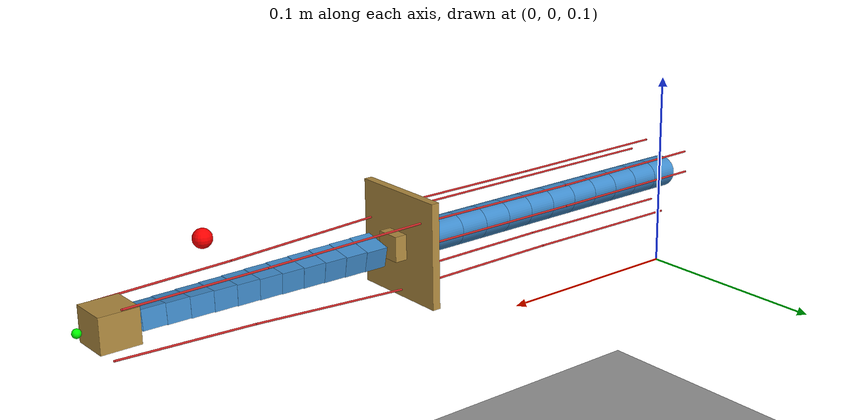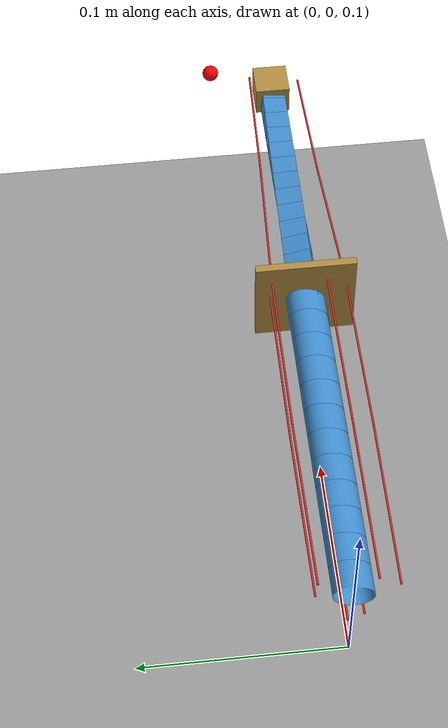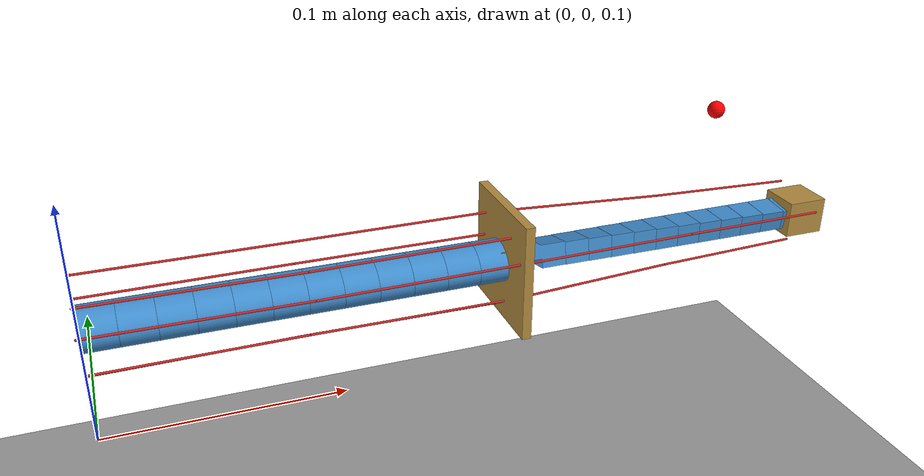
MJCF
<?xml version='1.0' encoding='utf-8'?>
<mujoco model="serial_tendon_family"><compiler angle="radian" autolimits="true" /><option timestep="0.0005" gravity="0 0 -9.8100000000000005" integrator="implicitfast" /><default><joint limited="false" /><geom contype="1" conaffinity="2" friction="0 0 0" /></default><asset><mesh name="near_cell_0_section" vertex="0 -0.01 2.4175425728033171e-18 0 -0.0099144486137381048 -0.001044209537760411 0 -0.0096592582628906853 -0.0020705523608201648 0 -0.0092387953251128682 -0.0030614674589207165 0 -0.0086602540378443883 -0.0039999999999999966 0 -0.0079335334029123541 -0.0048700914320697628 0 -0.0070710678118654779 -0.0056568542494923792 0 -0.0060876142900872076 -0.0063468267223298807 0 -0.0050000000000000018 -0.006928203230275507 0 -0.0038268343236509002 -0.0073910362600902932 0 -0.0025881904510252113 -0.0077274066103125453 0 -0.0013052619222005189 -0.0079315588909904828 0 -2.3207556918032139e-18 -0.0080000000000000002 0 0.0013052619222005124 -0.0079315588909904845 0 0.0025881904510252048 -0.0077274066103125471 0 0.0038268343236508942 -0.0073910362600902958 0 0.0049999999999999958 -0.0069282032302755113 0 0.0060876142900872024 -0.0063468267223298841 0 0.0070710678118654727 -0.0056568542494923818 0 0.0079335334029123506 -0.0048700914320697689 0 0.0086602540378443848 -0.0040000000000000044 0 0.0092387953251128682 -0.0030614674589207209 0 0.0096592582628906801 -0.0020705523608201704 0 0.0099144486137381048 -0.0010442095377604184 0 0.01 -3.2323185216375012e-18 0 0.0099144486137381048 0.0010442095377604095 0 0.0096592582628906836 0.0020705523608201613 0 0.00923879532511287 0.0030614674589207122 0 0.00866025403784439 0.0039999999999999949 0 0.0079335334029123541 0.0048700914320697619 0 0.0070710678118654797 0.0056568542494923758 0 0.0060876142900872102 0.0063468267223298781 0 0.0050000000000000062 0.0069282032302755078 0 0.003826834323650905 0.0073910362600902915 0 0.0025881904510252165 0.0077274066103125436 0 0.0013052619222005269 0.0079315588909904828 0 3.6217982987858192e-18 0.0080000000000000002 0 -0.0013052619222005107 0.0079315588909904845 0 -0.0025881904510252013 0.0077274066103125488 0 -0.0038268343236508911 0.0073910362600902967 0 -0.0049999999999999914 0.006928203230275513 0 -0.0060876142900871981 0.0063468267223298876 0 -0.0070710678118654719 0.0056568542494923836 0 -0.0079335334029123471 0.0048700914320697697 0 -0.0086602540378443848 0.0040000000000000053 0 -0.0092387953251128647 0.0030614674589207252 0 -0.0096592582628906819 0.0020705523608201748 0 -0.0099144486137381013 0.0010442095377604223 0.014166666666666668 -0.01 2.4175425728033171e-18 0.014166666666666668 -0.0099144486137381048 -0.001044209537760411 0.014166666666666668 -0.0096592582628906853 -0.0020705523608201648 0.014166666666666668 -0.0092387953251128682 -0.0030614674589207165 0.014166666666666668 -0.0086602540378443883 -0.0039999999999999966 0.014166666666666668 -0.0079335334029123541 -0.0048700914320697628 0.014166666666666668 -0.0070710678118654779 -0.0056568542494923792 0.014166666666666668 -0.0060876142900872076 -0.0063468267223298807 0.014166666666666668 -0.0050000000000000018 -0.006928203230275507 0.014166666666666668 -0.0038268343236509002 -0.0073910362600902932 0.014166666666666668 -0.0025881904510252113 -0.0077274066103125453 0.014166666666666668 -0.0013052619222005189 -0.0079315588909904828 0.014166666666666668 -2.3207556918032139e-18 -0.0080000000000000002 0.014166666666666668 0.0013052619222005124 -0.0079315588909904845 0.014166666666666668 0.0025881904510252048 -0.0077274066103125471 0.014166666666666668 0.0038268343236508942 -0.0073910362600902958 0.014166666666666668 0.0049999999999999958 -0.0069282032302755113 0.014166666666666668 0.0060876142900872024 -0.0063468267223298841 0.014166666666666668 0.0070710678118654727 -0.0056568542494923818 0.014166666666666668 0.0079335334029123506 -0.0048700914320697689 0.014166666666666668 0.0086602540378443848 -0.0040000000000000044 0.014166666666666668 0.0092387953251128682 -0.0030614674589207209 0.014166666666666668 0.0096592582628906801 -0.0020705523608201704 0.014166666666666668 0.0099144486137381048 -0.0010442095377604184 0.014166666666666668 0.01 -3.2323185216375012e-18 0.014166666666666668 0.0099144486137381048 0.0010442095377604095 0.014166666666666668 0.0096592582628906836 0.0020705523608201613 0.014166666666666668 0.00923879532511287 0.0030614674589207122 0.014166666666666668 0.00866025403784439 0.0039999999999999949 0.014166666666666668 0.0079335334029123541 0.0048700914320697619 0.014166666666666668 0.0070710678118654797 0.0056568542494923758 0.014166666666666668 0.0060876142900872102 0.0063468267223298781 0.014166666666666668 0.0050000000000000062 0.0069282032302755078 0.014166666666666668 0.003826834323650905 0.0073910362600902915 0.014166666666666668 0.0025881904510252165 0.0077274066103125436 0.014166666666666668 0.0013052619222005269 0.0079315588909904828 0.014166666666666668 3.6217982987858192e-18 0.0080000000000000002 0.014166666666666668 -0.0013052619222005107 0.0079315588909904845 0.014166666666666668 -0.0025881904510252013 0.0077274066103125488 0.014166666666666668 -0.0038268343236508911 0.0073910362600902967 0.014166666666666668 -0.0049999999999999914 0.006928203230275513 0.014166666666666668 -0.0060876142900871981 0.0063468267223298876 0.014166666666666668 -0.0070710678118654719 0.0056568542494923836 0.014166666666666668 -0.0079335334029123471 0.0048700914320697697 0.014166666666666668 -0.0086602540378443848 0.0040000000000000053 0.014166666666666668 -0.0092387953251128647 0.0030614674589207252 0.014166666666666668 -0.0096592582628906819 0.0020705523608201748 0.014166666666666668 -0.0099144486137381013 0.0010442095377604223" face="0 1 49 0 49 48 1 2 50 1 50 49 2 3 51 2 51 50 3 4 52 3 52 51 4 5 53 4 53 52 5 6 54 5 54 53 6 7 55 6 55 54 7 8 56 7 56 55 8 9 57 8 57 56 9 10 58 9 58 57 10 11 59 10 59 58 11 12 60 11 60 59 12 13 61 12 61 60 13 14 62 13 62 61 14 15 63 14 63 62 15 16 64 15 64 63 16 17 65 16 65 64 17 18 66 17 66 65 18 19 67 18 67 66 19 20 68 19 68 67 20 21 69 20 69 68 21 22 70 21 70 69 22 23 71 22 71 70 23 24 72 23 72 71 24 25 73 24 73 72 25 26 74 25 74 73 26 27 75 26 75 74 27 28 76 27 76 75 28 29 77 28 77 76 29 30 78 29 78 77 30 31 79 30 79 78 31 32 80 31 80 79 32 33 81 32 81 80 33 34 82 33 82 81 34 35 83 34 83 82 35 36 84 35 84 83 36 37 85 36 85 84 37 38 86 37 86 85 38 39 87 38 87 86 39 40 88 39 88 87 40 41 89 40 89 88 41 42 90 41 90 89 42 43 91 42 91 90 43 44 92 43 92 91 44 45 93 44 93 92 45 46 94 45 94 93 46 47 95 46 95 94 47 0 48 47 48 95" /><mesh name="near_cell_1_section" vertex="0 -0.01 2.4175425728033171e-18 0 -0.0099144486137381048 -0.001044209537760411 0 -0.0096592582628906853 -0.0020705523608201648 0 -0.0092387953251128682 -0.0030614674589207165 0 -0.0086602540378443883 -0.0039999999999999966 0 -0.0079335334029123541 -0.0048700914320697628 0 -0.0070710678118654779 -0.0056568542494923792 0 -0.0060876142900872076 -0.0063468267223298807 0 -0.0050000000000000018 -0.006928203230275507 0 -0.0038268343236509002 -0.0073910362600902932 0 -0.0025881904510252113 -0.0077274066103125453 0 -0.0013052619222005189 -0.0079315588909904828 0 -2.3207556918032139e-18 -0.0080000000000000002 0 0.0013052619222005124 -0.0079315588909904845 0 0.0025881904510252048 -0.0077274066103125471 0 0.0038268343236508942 -0.0073910362600902958 0 0.0049999999999999958 -0.0069282032302755113 0 0.0060876142900872024 -0.0063468267223298841 0 0.0070710678118654727 -0.0056568542494923818 0 0.0079335334029123506 -0.0048700914320697689 0 0.0086602540378443848 -0.0040000000000000044 0 0.0092387953251128682 -0.0030614674589207209 0 0.0096592582628906801 -0.0020705523608201704 0 0.0099144486137381048 -0.0010442095377604184 0 0.01 -3.2323185216375012e-18 0 0.0099144486137381048 0.0010442095377604095 0 0.0096592582628906836 0.0020705523608201613 0 0.00923879532511287 0.0030614674589207122 0 0.00866025403784439 0.0039999999999999949 0 0.0079335334029123541 0.0048700914320697619 0 0.0070710678118654797 0.0056568542494923758 0 0.0060876142900872102 0.0063468267223298781 0 0.0050000000000000062 0.0069282032302755078 0 0.003826834323650905 0.0073910362600902915 0 0.0025881904510252165 0.0077274066103125436 0 0.0013052619222005269 0.0079315588909904828 0 3.6217982987858192e-18 0.0080000000000000002 0 -0.0013052619222005107 0.0079315588909904845 0 -0.0025881904510252013 0.0077274066103125488 0 -0.0038268343236508911 0.0073910362600902967 0 -0.0049999999999999914 0.006928203230275513 0 -0.0060876142900871981 0.0063468267223298876 0 -0.0070710678118654719 0.0056568542494923836 0 -0.0079335334029123471 0.0048700914320697697 0 -0.0086602540378443848 0.0040000000000000053 0 -0.0092387953251128647 0.0030614674589207252 0 -0.0096592582628906819 0.0020705523608201748 0 -0.0099144486137381013 0.0010442095377604223 0.014166666666666668 -0.01 2.4175425728033171e-18 0.014166666666666668 -0.0099144486137381048 -0.001044209537760411 0.014166666666666668 -0.0096592582628906853 -0.0020705523608201648 0.014166666666666668 -0.0092387953251128682 -0.0030614674589207165 0.014166666666666668 -0.0086602540378443883 -0.0039999999999999966 0.014166666666666668 -0.0079335334029123541 -0.0048700914320697628 0.014166666666666668 -0.0070710678118654779 -0.0056568542494923792 0.014166666666666668 -0.0060876142900872076 -0.0063468267223298807 0.014166666666666668 -0.0050000000000000018 -0.006928203230275507 0.014166666666666668 -0.0038268343236509002 -0.0073910362600902932 0.014166666666666668 -0.0025881904510252113 -0.0077274066103125453 0.014166666666666668 -0.0013052619222005189 -0.0079315588909904828 0.014166666666666668 -2.3207556918032139e-18 -0.0080000000000000002 0.014166666666666668 0.0013052619222005124 -0.0079315588909904845 0.014166666666666668 0.0025881904510252048 -0.0077274066103125471 0.014166666666666668 0.0038268343236508942 -0.0073910362600902958 0.014166666666666668 0.0049999999999999958 -0.0069282032302755113 0.014166666666666668 0.0060876142900872024 -0.0063468267223298841 0.014166666666666668 0.0070710678118654727 -0.0056568542494923818 0.014166666666666668 0.0079335334029123506 -0.0048700914320697689 0.014166666666666668 0.0086602540378443848 -0.0040000000000000044 0.014166666666666668 0.0092387953251128682 -0.0030614674589207209 0.014166666666666668 0.0096592582628906801 -0.0020705523608201704 0.014166666666666668 0.0099144486137381048 -0.0010442095377604184 0.014166666666666668 0.01 -3.2323185216375012e-18 0.014166666666666668 0.0099144486137381048 0.0010442095377604095 0.014166666666666668 0.0096592582628906836 0.0020705523608201613 0.014166666666666668 0.00923879532511287 0.0030614674589207122 0.014166666666666668 0.00866025403784439 0.0039999999999999949 0.014166666666666668 0.0079335334029123541 0.0048700914320697619 0.014166666666666668 0.0070710678118654797 0.0056568542494923758 0.014166666666666668 0.0060876142900872102 0.0063468267223298781 0.014166666666666668 0.0050000000000000062 0.0069282032302755078 0.014166666666666668 0.003826834323650905 0.0073910362600902915 0.014166666666666668 0.0025881904510252165 0.0077274066103125436 0.014166666666666668 0.0013052619222005269 0.0079315588909904828 0.014166666666666668 3.6217982987858192e-18 0.0080000000000000002 0.014166666666666668 -0.0013052619222005107 0.0079315588909904845 0.014166666666666668 -0.0025881904510252013 0.0077274066103125488 0.014166666666666668 -0.0038268343236508911 0.0073910362600902967 0.014166666666666668 -0.0049999999999999914 0.006928203230275513 0.014166666666666668 -0.0060876142900871981 0.0063468267223298876 0.014166666666666668 -0.0070710678118654719 0.0056568542494923836 0.014166666666666668 -0.0079335334029123471 0.0048700914320697697 0.014166666666666668 -0.0086602540378443848 0.0040000000000000053 0.014166666666666668 -0.0092387953251128647 0.0030614674589207252 0.014166666666666668 -0.0096592582628906819 0.0020705523608201748 0.014166666666666668 -0.0099144486137381013 0.0010442095377604223" face="0 1 49 0 49 48 1 2 50 1 50 49 2 3 51 2 51 50 3 4 52 3 52 51 4 5 53 4 53 52 5 6 54 5 54 53 6 7 55 6 55 54 7 8 56 7 56 55 8 9 57 8 57 56 9 10 58 9 58 57 10 11 59 10 59 58 11 12 60 11 60 59 12 13 61 12 61 60 13 14 62 13 62 61 14 15 63 14 63 62 15 16 64 15 64 63 16 17 65 16 65 64 17 18 66 17 66 65 18 19 67 18 67 66 19 20 68 19 68 67 20 21 69 20 69 68 21 22 70 21 70 69 22 23 71 22 71 70 23 24 72 23 72 71 24 25 73 24 73 72 25 26 74 25 74 73 26 27 75 26 75 74 27 28 76 27 76 75 28 29 77 28 77 76 29 30 78 29 78 77 30 31 79 30 79 78 31 32 80 31 80 79 32 33 81 32 81 80 33 34 82 33 82 81 34 35 83 34 83 82 35 36 84 35 84 83 36 37 85 36 85 84 37 38 86 37 86 85 38 39 87 38 87 86 39 40 88 39 88 87 40 41 89 40 89 88 41 42 90 41 90 89 42 43 91 42 91 90 43 44 92 43 92 91 44 45 93 44 93 92 45 46 94 45 94 93 46 47 95 46 95 94 47 0 48 47 48 95" /><mesh name="near_cell_2_section" vertex="0 -0.01 2.4175425728033171e-18 0 -0.0099144486137381048 -0.001044209537760411 0 -0.0096592582628906853 -0.0020705523608201648 0 -0.0092387953251128682 -0.0030614674589207165 0 -0.0086602540378443883 -0.0039999999999999966 0 -0.0079335334029123541 -0.0048700914320697628 0 -0.0070710678118654779 -0.0056568542494923792 0 -0.0060876142900872076 -0.0063468267223298807 0 -0.0050000000000000018 -0.006928203230275507 0 -0.0038268343236509002 -0.0073910362600902932 0 -0.0025881904510252113 -0.0077274066103125453 0 -0.0013052619222005189 -0.0079315588909904828 0 -2.3207556918032139e-18 -0.0080000000000000002 0 0.0013052619222005124 -0.0079315588909904845 0 0.0025881904510252048 -0.0077274066103125471 0 0.0038268343236508942 -0.0073910362600902958 0 0.0049999999999999958 -0.0069282032302755113 0 0.0060876142900872024 -0.0063468267223298841 0 0.0070710678118654727 -0.0056568542494923818 0 0.0079335334029123506 -0.0048700914320697689 0 0.0086602540378443848 -0.0040000000000000044 0 0.0092387953251128682 -0.0030614674589207209 0 0.0096592582628906801 -0.0020705523608201704 0 0.0099144486137381048 -0.0010442095377604184 0 0.01 -3.2323185216375012e-18 0 0.0099144486137381048 0.0010442095377604095 0 0.0096592582628906836 0.0020705523608201613 0 0.00923879532511287 0.0030614674589207122 0 0.00866025403784439 0.0039999999999999949 0 0.0079335334029123541 0.0048700914320697619 0 0.0070710678118654797 0.0056568542494923758 0 0.0060876142900872102 0.0063468267223298781 0 0.0050000000000000062 0.0069282032302755078 0 0.003826834323650905 0.0073910362600902915 0 0.0025881904510252165 0.0077274066103125436 0 0.0013052619222005269 0.0079315588909904828 0 3.6217982987858192e-18 0.0080000000000000002 0 -0.0013052619222005107 0.0079315588909904845 0 -0.0025881904510252013 0.0077274066103125488 0 -0.0038268343236508911 0.0073910362600902967 0 -0.0049999999999999914 0.006928203230275513 0 -0.0060876142900871981 0.0063468267223298876 0 -0.0070710678118654719 0.0056568542494923836 0 -0.0079335334029123471 0.0048700914320697697 0 -0.0086602540378443848 0.0040000000000000053 0 -0.0092387953251128647 0.0030614674589207252 0 -0.0096592582628906819 0.0020705523608201748 0 -0.0099144486137381013 0.0010442095377604223 0.014166666666666668 -0.01 2.4175425728033171e-18 0.014166666666666668 -0.0099144486137381048 -0.001044209537760411 0.014166666666666668 -0.0096592582628906853 -0.0020705523608201648 0.014166666666666668 -0.0092387953251128682 -0.0030614674589207165 0.014166666666666668 -0.0086602540378443883 -0.0039999999999999966 0.014166666666666668 -0.0079335334029123541 -0.0048700914320697628 0.014166666666666668 -0.0070710678118654779 -0.0056568542494923792 0.014166666666666668 -0.0060876142900872076 -0.0063468267223298807 0.014166666666666668 -0.0050000000000000018 -0.006928203230275507 0.014166666666666668 -0.0038268343236509002 -0.0073910362600902932 0.014166666666666668 -0.0025881904510252113 -0.0077274066103125453 0.014166666666666668 -0.0013052619222005189 -0.0079315588909904828 0.014166666666666668 -2.3207556918032139e-18 -0.0080000000000000002 0.014166666666666668 0.0013052619222005124 -0.0079315588909904845 0.014166666666666668 0.0025881904510252048 -0.0077274066103125471 0.014166666666666668 0.0038268343236508942 -0.0073910362600902958 0.014166666666666668 0.0049999999999999958 -0.0069282032302755113 0.014166666666666668 0.0060876142900872024 -0.0063468267223298841 0.014166666666666668 0.0070710678118654727 -0.0056568542494923818 0.014166666666666668 0.0079335334029123506 -0.0048700914320697689 0.014166666666666668 0.0086602540378443848 -0.0040000000000000044 0.014166666666666668 0.0092387953251128682 -0.0030614674589207209 0.014166666666666668 0.0096592582628906801 -0.0020705523608201704 0.014166666666666668 0.0099144486137381048 -0.0010442095377604184 0.014166666666666668 0.01 -3.2323185216375012e-18 0.014166666666666668 0.0099144486137381048 0.0010442095377604095 0.014166666666666668 0.0096592582628906836 0.0020705523608201613 0.014166666666666668 0.00923879532511287 0.0030614674589207122 0.014166666666666668 0.00866025403784439 0.0039999999999999949 0.014166666666666668 0.0079335334029123541 0.0048700914320697619 0.014166666666666668 0.0070710678118654797 0.0056568542494923758 0.014166666666666668 0.0060876142900872102 0.0063468267223298781 0.014166666666666668 0.0050000000000000062 0.0069282032302755078 0.014166666666666668 0.003826834323650905 0.0073910362600902915 0.014166666666666668 0.0025881904510252165 0.0077274066103125436 0.014166666666666668 0.0013052619222005269 0.0079315588909904828 0.014166666666666668 3.6217982987858192e-18 0.0080000000000000002 0.014166666666666668 -0.0013052619222005107 0.0079315588909904845 0.014166666666666668 -0.0025881904510252013 0.0077274066103125488 0.014166666666666668 -0.0038268343236508911 0.0073910362600902967 0.014166666666666668 -0.0049999999999999914 0.006928203230275513 0.014166666666666668 -0.0060876142900871981 0.0063468267223298876 0.014166666666666668 -0.0070710678118654719 0.0056568542494923836 0.014166666666666668 -0.0079335334029123471 0.0048700914320697697 0.014166666666666668 -0.0086602540378443848 0.0040000000000000053 0.014166666666666668 -0.0092387953251128647 0.0030614674589207252 0.014166666666666668 -0.0096592582628906819 0.0020705523608201748 0.014166666666666668 -0.0099144486137381013 0.0010442095377604223" face="0 1 49 0 49 48 1 2 50 1 50 49 2 3 51 2 51 50 3 4 52 3 52 51 4 5 53 4 53 52 5 6 54 5 54 53 6 7 55 6 55 54 7 8 56 7 56 55 8 9 57 8 57 56 9 10 58 9 58 57 10 11 59 10 59 58 11 12 60 11 60 59 12 13 61 12 61 60 13 14 62 13 62 61 14 15 63 14 63 62 15 16 64 15 64 63 16 17 65 16 65 64 17 18 66 17 66 65 18 19 67 18 67 66 19 20 68 19 68 67 20 21 69 20 69 68 21 22 70 21 70 69 22 23 71 22 71 70 23 24 72 23 72 71 24 25 73 24 73 72 25 26 74 25 74 73 26 27 75 26 75 74 27 28 76 27 76 75 28 29 77 28 77 76 29 30 78 29 78 77 30 31 79 30 79 78 31 32 80 31 80 79 32 33 81 32 81 80 33 34 82 33 82 81 34 35 83 34 83 82 35 36 84 35 84 83 36 37 85 36 85 84 37 38 86 37 86 85 38 39 87 38 87 86 39 40 88 39 88 87 40 41 89 40 89 88 41 42 90 41 90 89 42 43 91 42 91 90 43 44 92 43 92 91 44 45 93 44 93 92 45 46 94 45 94 93 46 47 95 46 95 94 47 0 48 47 48 95" /><mesh name="near_cell_3_section" vertex="0 -0.01 2.4175425728033171e-18 0 -0.0099144486137381048 -0.001044209537760411 0 -0.0096592582628906853 -0.0020705523608201648 0 -0.0092387953251128682 -0.0030614674589207165 0 -0.0086602540378443883 -0.0039999999999999966 0 -0.0079335334029123541 -0.0048700914320697628 0 -0.0070710678118654779 -0.0056568542494923792 0 -0.0060876142900872076 -0.0063468267223298807 0 -0.0050000000000000018 -0.006928203230275507 0 -0.0038268343236509002 -0.0073910362600902932 0 -0.0025881904510252113 -0.0077274066103125453 0 -0.0013052619222005189 -0.0079315588909904828 0 -2.3207556918032139e-18 -0.0080000000000000002 0 0.0013052619222005124 -0.0079315588909904845 0 0.0025881904510252048 -0.0077274066103125471 0 0.0038268343236508942 -0.0073910362600902958 0 0.0049999999999999958 -0.0069282032302755113 0 0.0060876142900872024 -0.0063468267223298841 0 0.0070710678118654727 -0.0056568542494923818 0 0.0079335334029123506 -0.0048700914320697689 0 0.0086602540378443848 -0.0040000000000000044 0 0.0092387953251128682 -0.0030614674589207209 0 0.0096592582628906801 -0.0020705523608201704 0 0.0099144486137381048 -0.0010442095377604184 0 0.01 -3.2323185216375012e-18 0 0.0099144486137381048 0.0010442095377604095 0 0.0096592582628906836 0.0020705523608201613 0 0.00923879532511287 0.0030614674589207122 0 0.00866025403784439 0.0039999999999999949 0 0.0079335334029123541 0.0048700914320697619 0 0.0070710678118654797 0.0056568542494923758 0 0.0060876142900872102 0.0063468267223298781 0 0.0050000000000000062 0.0069282032302755078 0 0.003826834323650905 0.0073910362600902915 0 0.0025881904510252165 0.0077274066103125436 0 0.0013052619222005269 0.0079315588909904828 0 3.6217982987858192e-18 0.0080000000000000002 0 -0.0013052619222005107 0.0079315588909904845 0 -0.0025881904510252013 0.0077274066103125488 0 -0.0038268343236508911 0.0073910362600902967 0 -0.0049999999999999914 0.006928203230275513 0 -0.0060876142900871981 0.0063468267223298876 0 -0.0070710678118654719 0.0056568542494923836 0 -0.0079335334029123471 0.0048700914320697697 0 -0.0086602540378443848 0.0040000000000000053 0 -0.0092387953251128647 0.0030614674589207252 0 -0.0096592582628906819 0.0020705523608201748 0 -0.0099144486137381013 0.0010442095377604223 0.014166666666666668 -0.01 2.4175425728033171e-18 0.014166666666666668 -0.0099144486137381048 -0.001044209537760411 0.014166666666666668 -0.0096592582628906853 -0.0020705523608201648 0.014166666666666668 -0.0092387953251128682 -0.0030614674589207165 0.014166666666666668 -0.0086602540378443883 -0.0039999999999999966 0.014166666666666668 -0.0079335334029123541 -0.0048700914320697628 0.014166666666666668 -0.0070710678118654779 -0.0056568542494923792 0.014166666666666668 -0.0060876142900872076 -0.0063468267223298807 0.014166666666666668 -0.0050000000000000018 -0.006928203230275507 0.014166666666666668 -0.0038268343236509002 -0.0073910362600902932 0.014166666666666668 -0.0025881904510252113 -0.0077274066103125453 0.014166666666666668 -0.0013052619222005189 -0.0079315588909904828 0.014166666666666668 -2.3207556918032139e-18 -0.0080000000000000002 0.014166666666666668 0.0013052619222005124 -0.0079315588909904845 0.014166666666666668 0.0025881904510252048 -0.0077274066103125471 0.014166666666666668 0.0038268343236508942 -0.0073910362600902958 0.014166666666666668 0.0049999999999999958 -0.0069282032302755113 0.014166666666666668 0.0060876142900872024 -0.0063468267223298841 0.014166666666666668 0.0070710678118654727 -0.0056568542494923818 0.014166666666666668 0.0079335334029123506 -0.0048700914320697689 0.014166666666666668 0.0086602540378443848 -0.0040000000000000044 0.014166666666666668 0.0092387953251128682 -0.0030614674589207209 0.014166666666666668 0.0096592582628906801 -0.0020705523608201704 0.014166666666666668 0.0099144486137381048 -0.0010442095377604184 0.014166666666666668 0.01 -3.2323185216375012e-18 0.014166666666666668 0.0099144486137381048 0.0010442095377604095 0.014166666666666668 0.0096592582628906836 0.0020705523608201613 0.014166666666666668 0.00923879532511287 0.0030614674589207122 0.014166666666666668 0.00866025403784439 0.0039999999999999949 0.014166666666666668 0.0079335334029123541 0.0048700914320697619 0.014166666666666668 0.0070710678118654797 0.0056568542494923758 0.014166666666666668 0.0060876142900872102 0.0063468267223298781 0.014166666666666668 0.0050000000000000062 0.0069282032302755078 0.014166666666666668 0.003826834323650905 0.0073910362600902915 0.014166666666666668 0.0025881904510252165 0.0077274066103125436 0.014166666666666668 0.0013052619222005269 0.0079315588909904828 0.014166666666666668 3.6217982987858192e-18 0.0080000000000000002 0.014166666666666668 -0.0013052619222005107 0.0079315588909904845 0.014166666666666668 -0.0025881904510252013 0.0077274066103125488 0.014166666666666668 -0.0038268343236508911 0.0073910362600902967 0.014166666666666668 -0.0049999999999999914 0.006928203230275513 0.014166666666666668 -0.0060876142900871981 0.0063468267223298876 0.014166666666666668 -0.0070710678118654719 0.0056568542494923836 0.014166666666666668 -0.0079335334029123471 0.0048700914320697697 0.014166666666666668 -0.0086602540378443848 0.0040000000000000053 0.014166666666666668 -0.0092387953251128647 0.0030614674589207252 0.014166666666666668 -0.0096592582628906819 0.0020705523608201748 0.014166666666666668 -0.0099144486137381013 0.0010442095377604223" face="0 1 49 0 49 48 1 2 50 1 50 49 2 3 51 2 51 50 3 4 52 3 52 51 4 5 53 4 53 52 5 6 54 5 54 53 6 7 55 6 55 54 7 8 56 7 56 55 8 9 57 8 57 56 9 10 58 9 58 57 10 11 59 10 59 58 11 12 60 11 60 59 12 13 61 12 61 60 13 14 62 13 62 61 14 15 63 14 63 62 15 16 64 15 64 63 16 17 65 16 65 64 17 18 66 17 66 65 18 19 67 18 67 66 19 20 68 19 68 67 20 21 69 20 69 68 21 22 70 21 70 69 22 23 71 22 71 70 23 24 72 23 72 71 24 25 73 24 73 72 25 26 74 25 74 73 26 27 75 26 75 74 27 28 76 27 76 75 28 29 77 28 77 76 29 30 78 29 78 77 30 31 79 30 79 78 31 32 80 31 80 79 32 33 81 32 81 80 33 34 82 33 82 81 34 35 83 34 83 82 35 36 84 35 84 83 36 37 85 36 85 84 37 38 86 37 86 85 38 39 87 38 87 86 39 40 88 39 88 87 40 41 89 40 89 88 41 42 90 41 90 89 42 43 91 42 91 90 43 44 92 43 92 91 44 45 93 44 93 92 45 46 94 45 94 93 46 47 95 46 95 94 47 0 48 47 48 95" /><mesh name="near_cell_4_section" vertex="0 -0.01 2.4175425728033171e-18 0 -0.0099144486137381048 -0.001044209537760411 0 -0.0096592582628906853 -0.0020705523608201648 0 -0.0092387953251128682 -0.0030614674589207165 0 -0.0086602540378443883 -0.0039999999999999966 0 -0.0079335334029123541 -0.0048700914320697628 0 -0.0070710678118654779 -0.0056568542494923792 0 -0.0060876142900872076 -0.0063468267223298807 0 -0.0050000000000000018 -0.006928203230275507 0 -0.0038268343236509002 -0.0073910362600902932 0 -0.0025881904510252113 -0.0077274066103125453 0 -0.0013052619222005189 -0.0079315588909904828 0 -2.3207556918032139e-18 -0.0080000000000000002 0 0.0013052619222005124 -0.0079315588909904845 0 0.0025881904510252048 -0.0077274066103125471 0 0.0038268343236508942 -0.0073910362600902958 0 0.0049999999999999958 -0.0069282032302755113 0 0.0060876142900872024 -0.0063468267223298841 0 0.0070710678118654727 -0.0056568542494923818 0 0.0079335334029123506 -0.0048700914320697689 0 0.0086602540378443848 -0.0040000000000000044 0 0.0092387953251128682 -0.0030614674589207209 0 0.0096592582628906801 -0.0020705523608201704 0 0.0099144486137381048 -0.0010442095377604184 0 0.01 -3.2323185216375012e-18 0 0.0099144486137381048 0.0010442095377604095 0 0.0096592582628906836 0.0020705523608201613 0 0.00923879532511287 0.0030614674589207122 0 0.00866025403784439 0.0039999999999999949 0 0.0079335334029123541 0.0048700914320697619 0 0.0070710678118654797 0.0056568542494923758 0 0.0060876142900872102 0.0063468267223298781 0 0.0050000000000000062 0.0069282032302755078 0 0.003826834323650905 0.0073910362600902915 0 0.0025881904510252165 0.0077274066103125436 0 0.0013052619222005269 0.0079315588909904828 0 3.6217982987858192e-18 0.0080000000000000002 0 -0.0013052619222005107 0.0079315588909904845 0 -0.0025881904510252013 0.0077274066103125488 0 -0.0038268343236508911 0.0073910362600902967 0 -0.0049999999999999914 0.006928203230275513 0 -0.0060876142900871981 0.0063468267223298876 0 -0.0070710678118654719 0.0056568542494923836 0 -0.0079335334029123471 0.0048700914320697697 0 -0.0086602540378443848 0.0040000000000000053 0 -0.0092387953251128647 0.0030614674589207252 0 -0.0096592582628906819 0.0020705523608201748 0 -0.0099144486137381013 0.0010442095377604223 0.014166666666666668 -0.01 2.4175425728033171e-18 0.014166666666666668 -0.0099144486137381048 -0.001044209537760411 0.014166666666666668 -0.0096592582628906853 -0.0020705523608201648 0.014166666666666668 -0.0092387953251128682 -0.0030614674589207165 0.014166666666666668 -0.0086602540378443883 -0.0039999999999999966 0.014166666666666668 -0.0079335334029123541 -0.0048700914320697628 0.014166666666666668 -0.0070710678118654779 -0.0056568542494923792 0.014166666666666668 -0.0060876142900872076 -0.0063468267223298807 0.014166666666666668 -0.0050000000000000018 -0.006928203230275507 0.014166666666666668 -0.0038268343236509002 -0.0073910362600902932 0.014166666666666668 -0.0025881904510252113 -0.0077274066103125453 0.014166666666666668 -0.0013052619222005189 -0.0079315588909904828 0.014166666666666668 -2.3207556918032139e-18 -0.0080000000000000002 0.014166666666666668 0.0013052619222005124 -0.0079315588909904845 0.014166666666666668 0.0025881904510252048 -0.0077274066103125471 0.014166666666666668 0.0038268343236508942 -0.0073910362600902958 0.014166666666666668 0.0049999999999999958 -0.0069282032302755113 0.014166666666666668 0.0060876142900872024 -0.0063468267223298841 0.014166666666666668 0.0070710678118654727 -0.0056568542494923818 0.014166666666666668 0.0079335334029123506 -0.0048700914320697689 0.014166666666666668 0.0086602540378443848 -0.0040000000000000044 0.014166666666666668 0.0092387953251128682 -0.0030614674589207209 0.014166666666666668 0.0096592582628906801 -0.0020705523608201704 0.014166666666666668 0.0099144486137381048 -0.0010442095377604184 0.014166666666666668 0.01 -3.2323185216375012e-18 0.014166666666666668 0.0099144486137381048 0.0010442095377604095 0.014166666666666668 0.0096592582628906836 0.0020705523608201613 0.014166666666666668 0.00923879532511287 0.0030614674589207122 0.014166666666666668 0.00866025403784439 0.0039999999999999949 0.014166666666666668 0.0079335334029123541 0.0048700914320697619 0.014166666666666668 0.0070710678118654797 0.0056568542494923758 0.014166666666666668 0.0060876142900872102 0.0063468267223298781 0.014166666666666668 0.0050000000000000062 0.0069282032302755078 0.014166666666666668 0.003826834323650905 0.0073910362600902915 0.014166666666666668 0.0025881904510252165 0.0077274066103125436 0.014166666666666668 0.0013052619222005269 0.0079315588909904828 0.014166666666666668 3.6217982987858192e-18 0.0080000000000000002 0.014166666666666668 -0.0013052619222005107 0.0079315588909904845 0.014166666666666668 -0.0025881904510252013 0.0077274066103125488 0.014166666666666668 -0.0038268343236508911 0.0073910362600902967 0.014166666666666668 -0.0049999999999999914 0.006928203230275513 0.014166666666666668 -0.0060876142900871981 0.0063468267223298876 0.014166666666666668 -0.0070710678118654719 0.0056568542494923836 0.014166666666666668 -0.0079335334029123471 0.0048700914320697697 0.014166666666666668 -0.0086602540378443848 0.0040000000000000053 0.014166666666666668 -0.0092387953251128647 0.0030614674589207252 0.014166666666666668 -0.0096592582628906819 0.0020705523608201748 0.014166666666666668 -0.0099144486137381013 0.0010442095377604223" face="0 1 49 0 49 48 1 2 50 1 50 49 2 3 51 2 51 50 3 4 52 3 52 51 4 5 53 4 53 52 5 6 54 5 54 53 6 7 55 6 55 54 7 8 56 7 56 55 8 9 57 8 57 56 9 10 58 9 58 57 10 11 59 10 59 58 11 12 60 11 60 59 12 13 61 12 61 60 13 14 62 13 62 61 14 15 63 14 63 62 15 16 64 15 64 63 16 17 65 16 65 64 17 18 66 17 66 65 18 19 67 18 67 66 19 20 68 19 68 67 20 21 69 20 69 68 21 22 70 21 70 69 22 23 71 22 71 70 23 24 72 23 72 71 24 25 73 24 73 72 25 26 74 25 74 73 26 27 75 26 75 74 27 28 76 27 76 75 28 29 77 28 77 76 29 30 78 29 78 77 30 31 79 30 79 78 31 32 80 31 80 79 32 33 81 32 81 80 33 34 82 33 82 81 34 35 83 34 83 82 35 36 84 35 84 83 36 37 85 36 85 84 37 38 86 37 86 85 38 39 87 38 87 86 39 40 88 39 88 87 40 41 89 40 89 88 41 42 90 41 90 89 42 43 91 42 91 90 43 44 92 43 92 91 44 45 93 44 93 92 45 46 94 45 94 93 46 47 95 46 95 94 47 0 48 47 48 95" /><mesh name="near_cell_5_section" vertex="0 -0.01 2.4175425728033171e-18 0 -0.0099144486137381048 -0.001044209537760411 0 -0.0096592582628906853 -0.0020705523608201648 0 -0.0092387953251128682 -0.0030614674589207165 0 -0.0086602540378443883 -0.0039999999999999966 0 -0.0079335334029123541 -0.0048700914320697628 0 -0.0070710678118654779 -0.0056568542494923792 0 -0.0060876142900872076 -0.0063468267223298807 0 -0.0050000000000000018 -0.006928203230275507 0 -0.0038268343236509002 -0.0073910362600902932 0 -0.0025881904510252113 -0.0077274066103125453 0 -0.0013052619222005189 -0.0079315588909904828 0 -2.3207556918032139e-18 -0.0080000000000000002 0 0.0013052619222005124 -0.0079315588909904845 0 0.0025881904510252048 -0.0077274066103125471 0 0.0038268343236508942 -0.0073910362600902958 0 0.0049999999999999958 -0.0069282032302755113 0 0.0060876142900872024 -0.0063468267223298841 0 0.0070710678118654727 -0.0056568542494923818 0 0.0079335334029123506 -0.0048700914320697689 0 0.0086602540378443848 -0.0040000000000000044 0 0.0092387953251128682 -0.0030614674589207209 0 0.0096592582628906801 -0.0020705523608201704 0 0.0099144486137381048 -0.0010442095377604184 0 0.01 -3.2323185216375012e-18 0 0.0099144486137381048 0.0010442095377604095 0 0.0096592582628906836 0.0020705523608201613 0 0.00923879532511287 0.0030614674589207122 0 0.00866025403784439 0.0039999999999999949 0 0.0079335334029123541 0.0048700914320697619 0 0.0070710678118654797 0.0056568542494923758 0 0.0060876142900872102 0.0063468267223298781 0 0.0050000000000000062 0.0069282032302755078 0 0.003826834323650905 0.0073910362600902915 0 0.0025881904510252165 0.0077274066103125436 0 0.0013052619222005269 0.0079315588909904828 0 3.6217982987858192e-18 0.0080000000000000002 0 -0.0013052619222005107 0.0079315588909904845 0 -0.0025881904510252013 0.0077274066103125488 0 -0.0038268343236508911 0.0073910362600902967 0 -0.0049999999999999914 0.006928203230275513 0 -0.0060876142900871981 0.0063468267223298876 0 -0.0070710678118654719 0.0056568542494923836 0 -0.0079335334029123471 0.0048700914320697697 0 -0.0086602540378443848 0.0040000000000000053 0 -0.0092387953251128647 0.0030614674589207252 0 -0.0096592582628906819 0.0020705523608201748 0 -0.0099144486137381013 0.0010442095377604223 0.014166666666666668 -0.01 2.4175425728033171e-18 0.014166666666666668 -0.0099144486137381048 -0.001044209537760411 0.014166666666666668 -0.0096592582628906853 -0.0020705523608201648 0.014166666666666668 -0.0092387953251128682 -0.0030614674589207165 0.014166666666666668 -0.0086602540378443883 -0.0039999999999999966 0.014166666666666668 -0.0079335334029123541 -0.0048700914320697628 0.014166666666666668 -0.0070710678118654779 -0.0056568542494923792 0.014166666666666668 -0.0060876142900872076 -0.0063468267223298807 0.014166666666666668 -0.0050000000000000018 -0.006928203230275507 0.014166666666666668 -0.0038268343236509002 -0.0073910362600902932 0.014166666666666668 -0.0025881904510252113 -0.0077274066103125453 0.014166666666666668 -0.0013052619222005189 -0.0079315588909904828 0.014166666666666668 -2.3207556918032139e-18 -0.0080000000000000002 0.014166666666666668 0.0013052619222005124 -0.0079315588909904845 0.014166666666666668 0.0025881904510252048 -0.0077274066103125471 0.014166666666666668 0.0038268343236508942 -0.0073910362600902958 0.014166666666666668 0.0049999999999999958 -0.0069282032302755113 0.014166666666666668 0.0060876142900872024 -0.0063468267223298841 0.014166666666666668 0.0070710678118654727 -0.0056568542494923818 0.014166666666666668 0.0079335334029123506 -0.0048700914320697689 0.014166666666666668 0.0086602540378443848 -0.0040000000000000044 0.014166666666666668 0.0092387953251128682 -0.0030614674589207209 0.014166666666666668 0.0096592582628906801 -0.0020705523608201704 0.014166666666666668 0.0099144486137381048 -0.0010442095377604184 0.014166666666666668 0.01 -3.2323185216375012e-18 0.014166666666666668 0.0099144486137381048 0.0010442095377604095 0.014166666666666668 0.0096592582628906836 0.0020705523608201613 0.014166666666666668 0.00923879532511287 0.0030614674589207122 0.014166666666666668 0.00866025403784439 0.0039999999999999949 0.014166666666666668 0.0079335334029123541 0.0048700914320697619 0.014166666666666668 0.0070710678118654797 0.0056568542494923758 0.014166666666666668 0.0060876142900872102 0.0063468267223298781 0.014166666666666668 0.0050000000000000062 0.0069282032302755078 0.014166666666666668 0.003826834323650905 0.0073910362600902915 0.014166666666666668 0.0025881904510252165 0.0077274066103125436 0.014166666666666668 0.0013052619222005269 0.0079315588909904828 0.014166666666666668 3.6217982987858192e-18 0.0080000000000000002 0.014166666666666668 -0.0013052619222005107 0.0079315588909904845 0.014166666666666668 -0.0025881904510252013 0.0077274066103125488 0.014166666666666668 -0.0038268343236508911 0.0073910362600902967 0.014166666666666668 -0.0049999999999999914 0.006928203230275513 0.014166666666666668 -0.0060876142900871981 0.0063468267223298876 0.014166666666666668 -0.0070710678118654719 0.0056568542494923836 0.014166666666666668 -0.0079335334029123471 0.0048700914320697697 0.014166666666666668 -0.0086602540378443848 0.0040000000000000053 0.014166666666666668 -0.0092387953251128647 0.0030614674589207252 0.014166666666666668 -0.0096592582628906819 0.0020705523608201748 0.014166666666666668 -0.0099144486137381013 0.0010442095377604223" face="0 1 49 0 49 48 1 2 50 1 50 49 2 3 51 2 51 50 3 4 52 3 52 51 4 5 53 4 53 52 5 6 54 5 54 53 6 7 55 6 55 54 7 8 56 7 56 55 8 9 57 8 57 56 9 10 58 9 58 57 10 11 59 10 59 58 11 12 60 11 60 59 12 13 61 12 61 60 13 14 62 13 62 61 14 15 63 14 63 62 15 16 64 15 64 63 16 17 65 16 65 64 17 18 66 17 66 65 18 19 67 18 67 66 19 20 68 19 68 67 20 21 69 20 69 68 21 22 70 21 70 69 22 23 71 22 71 70 23 24 72 23 72 71 24 25 73 24 73 72 25 26 74 25 74 73 26 27 75 26 75 74 27 28 76 27 76 75 28 29 77 28 77 76 29 30 78 29 78 77 30 31 79 30 79 78 31 32 80 31 80 79 32 33 81 32 81 80 33 34 82 33 82 81 34 35 83 34 83 82 35 36 84 35 84 83 36 37 85 36 85 84 37 38 86 37 86 85 38 39 87 38 87 86 39 40 88 39 88 87 40 41 89 40 89 88 41 42 90 41 90 89 42 43 91 42 91 90 43 44 92 43 92 91 44 45 93 44 93 92 45 46 94 45 94 93 46 47 95 46 95 94 47 0 48 47 48 95" /><mesh name="near_cell_6_section" vertex="0 -0.01 2.4175425728033171e-18 0 -0.0099144486137381048 -0.001044209537760411 0 -0.0096592582628906853 -0.0020705523608201648 0 -0.0092387953251128682 -0.0030614674589207165 0 -0.0086602540378443883 -0.0039999999999999966 0 -0.0079335334029123541 -0.0048700914320697628 0 -0.0070710678118654779 -0.0056568542494923792 0 -0.0060876142900872076 -0.0063468267223298807 0 -0.0050000000000000018 -0.006928203230275507 0 -0.0038268343236509002 -0.0073910362600902932 0 -0.0025881904510252113 -0.0077274066103125453 0 -0.0013052619222005189 -0.0079315588909904828 0 -2.3207556918032139e-18 -0.0080000000000000002 0 0.0013052619222005124 -0.0079315588909904845 0 0.0025881904510252048 -0.0077274066103125471 0 0.0038268343236508942 -0.0073910362600902958 0 0.0049999999999999958 -0.0069282032302755113 0 0.0060876142900872024 -0.0063468267223298841 0 0.0070710678118654727 -0.0056568542494923818 0 0.0079335334029123506 -0.0048700914320697689 0 0.0086602540378443848 -0.0040000000000000044 0 0.0092387953251128682 -0.0030614674589207209 0 0.0096592582628906801 -0.0020705523608201704 0 0.0099144486137381048 -0.0010442095377604184 0 0.01 -3.2323185216375012e-18 0 0.0099144486137381048 0.0010442095377604095 0 0.0096592582628906836 0.0020705523608201613 0 0.00923879532511287 0.0030614674589207122 0 0.00866025403784439 0.0039999999999999949 0 0.0079335334029123541 0.0048700914320697619 0 0.0070710678118654797 0.0056568542494923758 0 0.0060876142900872102 0.0063468267223298781 0 0.0050000000000000062 0.0069282032302755078 0 0.003826834323650905 0.0073910362600902915 0 0.0025881904510252165 0.0077274066103125436 0 0.0013052619222005269 0.0079315588909904828 0 3.6217982987858192e-18 0.0080000000000000002 0 -0.0013052619222005107 0.0079315588909904845 0 -0.0025881904510252013 0.0077274066103125488 0 -0.0038268343236508911 0.0073910362600902967 0 -0.0049999999999999914 0.006928203230275513 0 -0.0060876142900871981 0.0063468267223298876 0 -0.0070710678118654719 0.0056568542494923836 0 -0.0079335334029123471 0.0048700914320697697 0 -0.0086602540378443848 0.0040000000000000053 0 -0.0092387953251128647 0.0030614674589207252 0 -0.0096592582628906819 0.0020705523608201748 0 -0.0099144486137381013 0.0010442095377604223 0.014166666666666668 -0.01 2.4175425728033171e-18 0.014166666666666668 -0.0099144486137381048 -0.001044209537760411 0.014166666666666668 -0.0096592582628906853 -0.0020705523608201648 0.014166666666666668 -0.0092387953251128682 -0.0030614674589207165 0.014166666666666668 -0.0086602540378443883 -0.0039999999999999966 0.014166666666666668 -0.0079335334029123541 -0.0048700914320697628 0.014166666666666668 -0.0070710678118654779 -0.0056568542494923792 0.014166666666666668 -0.0060876142900872076 -0.0063468267223298807 0.014166666666666668 -0.0050000000000000018 -0.006928203230275507 0.014166666666666668 -0.0038268343236509002 -0.0073910362600902932 0.014166666666666668 -0.0025881904510252113 -0.0077274066103125453 0.014166666666666668 -0.0013052619222005189 -0.0079315588909904828 0.014166666666666668 -2.3207556918032139e-18 -0.0080000000000000002 0.014166666666666668 0.0013052619222005124 -0.0079315588909904845 0.014166666666666668 0.0025881904510252048 -0.0077274066103125471 0.014166666666666668 0.0038268343236508942 -0.0073910362600902958 0.014166666666666668 0.0049999999999999958 -0.0069282032302755113 0.014166666666666668 0.0060876142900872024 -0.0063468267223298841 0.014166666666666668 0.0070710678118654727 -0.0056568542494923818 0.014166666666666668 0.0079335334029123506 -0.0048700914320697689 0.014166666666666668 0.0086602540378443848 -0.0040000000000000044 0.014166666666666668 0.0092387953251128682 -0.0030614674589207209 0.014166666666666668 0.0096592582628906801 -0.0020705523608201704 0.014166666666666668 0.0099144486137381048 -0.0010442095377604184 0.014166666666666668 0.01 -3.2323185216375012e-18 0.014166666666666668 0.0099144486137381048 0.0010442095377604095 0.014166666666666668 0.0096592582628906836 0.0020705523608201613 0.014166666666666668 0.00923879532511287 0.0030614674589207122 0.014166666666666668 0.00866025403784439 0.0039999999999999949 0.014166666666666668 0.0079335334029123541 0.0048700914320697619 0.014166666666666668 0.0070710678118654797 0.0056568542494923758 0.014166666666666668 0.0060876142900872102 0.0063468267223298781 0.014166666666666668 0.0050000000000000062 0.0069282032302755078 0.014166666666666668 0.003826834323650905 0.0073910362600902915 0.014166666666666668 0.0025881904510252165 0.0077274066103125436 0.014166666666666668 0.0013052619222005269 0.0079315588909904828 0.014166666666666668 3.6217982987858192e-18 0.0080000000000000002 0.014166666666666668 -0.0013052619222005107 0.0079315588909904845 0.014166666666666668 -0.0025881904510252013 0.0077274066103125488 0.014166666666666668 -0.0038268343236508911 0.0073910362600902967 0.014166666666666668 -0.0049999999999999914 0.006928203230275513 0.014166666666666668 -0.0060876142900871981 0.0063468267223298876 0.014166666666666668 -0.0070710678118654719 0.0056568542494923836 0.014166666666666668 -0.0079335334029123471 0.0048700914320697697 0.014166666666666668 -0.0086602540378443848 0.0040000000000000053 0.014166666666666668 -0.0092387953251128647 0.0030614674589207252 0.014166666666666668 -0.0096592582628906819 0.0020705523608201748 0.014166666666666668 -0.0099144486137381013 0.0010442095377604223" face="0 1 49 0 49 48 1 2 50 1 50 49 2 3 51 2 51 50 3 4 52 3 52 51 4 5 53 4 53 52 5 6 54 5 54 53 6 7 55 6 55 54 7 8 56 7 56 55 8 9 57 8 57 56 9 10 58 9 58 57 10 11 59 10 59 58 11 12 60 11 60 59 12 13 61 12 61 60 13 14 62 13 62 61 14 15 63 14 63 62 15 16 64 15 64 63 16 17 65 16 65 64 17 18 66 17 66 65 18 19 67 18 67 66 19 20 68 19 68 67 20 21 69 20 69 68 21 22 70 21 70 69 22 23 71 22 71 70 23 24 72 23 72 71 24 25 73 24 73 72 25 26 74 25 74 73 26 27 75 26 75 74 27 28 76 27 76 75 28 29 77 28 77 76 29 30 78 29 78 77 30 31 79 30 79 78 31 32 80 31 80 79 32 33 81 32 81 80 33 34 82 33 82 81 34 35 83 34 83 82 35 36 84 35 84 83 36 37 85 36 85 84 37 38 86 37 86 85 38 39 87 38 87 86 39 40 88 39 88 87 40 41 89 40 89 88 41 42 90 41 90 89 42 43 91 42 91 90 43 44 92 43 92 91 44 45 93 44 93 92 45 46 94 45 94 93 46 47 95 46 95 94 47 0 48 47 48 95" /><mesh name="near_cell_7_section" vertex="0 -0.01 2.4175425728033171e-18 0 -0.0099144486137381048 -0.001044209537760411 0 -0.0096592582628906853 -0.0020705523608201648 0 -0.0092387953251128682 -0.0030614674589207165 0 -0.0086602540378443883 -0.0039999999999999966 0 -0.0079335334029123541 -0.0048700914320697628 0 -0.0070710678118654779 -0.0056568542494923792 0 -0.0060876142900872076 -0.0063468267223298807 0 -0.0050000000000000018 -0.006928203230275507 0 -0.0038268343236509002 -0.0073910362600902932 0 -0.0025881904510252113 -0.0077274066103125453 0 -0.0013052619222005189 -0.0079315588909904828 0 -2.3207556918032139e-18 -0.0080000000000000002 0 0.0013052619222005124 -0.0079315588909904845 0 0.0025881904510252048 -0.0077274066103125471 0 0.0038268343236508942 -0.0073910362600902958 0 0.0049999999999999958 -0.0069282032302755113 0 0.0060876142900872024 -0.0063468267223298841 0 0.0070710678118654727 -0.0056568542494923818 0 0.0079335334029123506 -0.0048700914320697689 0 0.0086602540378443848 -0.0040000000000000044 0 0.0092387953251128682 -0.0030614674589207209 0 0.0096592582628906801 -0.0020705523608201704 0 0.0099144486137381048 -0.0010442095377604184 0 0.01 -3.2323185216375012e-18 0 0.0099144486137381048 0.0010442095377604095 0 0.0096592582628906836 0.0020705523608201613 0 0.00923879532511287 0.0030614674589207122 0 0.00866025403784439 0.0039999999999999949 0 0.0079335334029123541 0.0048700914320697619 0 0.0070710678118654797 0.0056568542494923758 0 0.0060876142900872102 0.0063468267223298781 0 0.0050000000000000062 0.0069282032302755078 0 0.003826834323650905 0.0073910362600902915 0 0.0025881904510252165 0.0077274066103125436 0 0.0013052619222005269 0.0079315588909904828 0 3.6217982987858192e-18 0.0080000000000000002 0 -0.0013052619222005107 0.0079315588909904845 0 -0.0025881904510252013 0.0077274066103125488 0 -0.0038268343236508911 0.0073910362600902967 0 -0.0049999999999999914 0.006928203230275513 0 -0.0060876142900871981 0.0063468267223298876 0 -0.0070710678118654719 0.0056568542494923836 0 -0.0079335334029123471 0.0048700914320697697 0 -0.0086602540378443848 0.0040000000000000053 0 -0.0092387953251128647 0.0030614674589207252 0 -0.0096592582628906819 0.0020705523608201748 0 -0.0099144486137381013 0.0010442095377604223 0.014166666666666668 -0.01 2.4175425728033171e-18 0.014166666666666668 -0.0099144486137381048 -0.001044209537760411 0.014166666666666668 -0.0096592582628906853 -0.0020705523608201648 0.014166666666666668 -0.0092387953251128682 -0.0030614674589207165 0.014166666666666668 -0.0086602540378443883 -0.0039999999999999966 0.014166666666666668 -0.0079335334029123541 -0.0048700914320697628 0.014166666666666668 -0.0070710678118654779 -0.0056568542494923792 0.014166666666666668 -0.0060876142900872076 -0.0063468267223298807 0.014166666666666668 -0.0050000000000000018 -0.006928203230275507 0.014166666666666668 -0.0038268343236509002 -0.0073910362600902932 0.014166666666666668 -0.0025881904510252113 -0.0077274066103125453 0.014166666666666668 -0.0013052619222005189 -0.0079315588909904828 0.014166666666666668 -2.3207556918032139e-18 -0.0080000000000000002 0.014166666666666668 0.0013052619222005124 -0.0079315588909904845 0.014166666666666668 0.0025881904510252048 -0.0077274066103125471 0.014166666666666668 0.0038268343236508942 -0.0073910362600902958 0.014166666666666668 0.0049999999999999958 -0.0069282032302755113 0.014166666666666668 0.0060876142900872024 -0.0063468267223298841 0.014166666666666668 0.0070710678118654727 -0.0056568542494923818 0.014166666666666668 0.0079335334029123506 -0.0048700914320697689 0.014166666666666668 0.0086602540378443848 -0.0040000000000000044 0.014166666666666668 0.0092387953251128682 -0.0030614674589207209 0.014166666666666668 0.0096592582628906801 -0.0020705523608201704 0.014166666666666668 0.0099144486137381048 -0.0010442095377604184 0.014166666666666668 0.01 -3.2323185216375012e-18 0.014166666666666668 0.0099144486137381048 0.0010442095377604095 0.014166666666666668 0.0096592582628906836 0.0020705523608201613 0.014166666666666668 0.00923879532511287 0.0030614674589207122 0.014166666666666668 0.00866025403784439 0.0039999999999999949 0.014166666666666668 0.0079335334029123541 0.0048700914320697619 0.014166666666666668 0.0070710678118654797 0.0056568542494923758 0.014166666666666668 0.0060876142900872102 0.0063468267223298781 0.014166666666666668 0.0050000000000000062 0.0069282032302755078 0.014166666666666668 0.003826834323650905 0.0073910362600902915 0.014166666666666668 0.0025881904510252165 0.0077274066103125436 0.014166666666666668 0.0013052619222005269 0.0079315588909904828 0.014166666666666668 3.6217982987858192e-18 0.0080000000000000002 0.014166666666666668 -0.0013052619222005107 0.0079315588909904845 0.014166666666666668 -0.0025881904510252013 0.0077274066103125488 0.014166666666666668 -0.0038268343236508911 0.0073910362600902967 0.014166666666666668 -0.0049999999999999914 0.006928203230275513 0.014166666666666668 -0.0060876142900871981 0.0063468267223298876 0.014166666666666668 -0.0070710678118654719 0.0056568542494923836 0.014166666666666668 -0.0079335334029123471 0.0048700914320697697 0.014166666666666668 -0.0086602540378443848 0.0040000000000000053 0.014166666666666668 -0.0092387953251128647 0.0030614674589207252 0.014166666666666668 -0.0096592582628906819 0.0020705523608201748 0.014166666666666668 -0.0099144486137381013 0.0010442095377604223" face="0 1 49 0 49 48 1 2 50 1 50 49 2 3 51 2 51 50 3 4 52 3 52 51 4 5 53 4 53 52 5 6 54 5 54 53 6 7 55 6 55 54 7 8 56 7 56 55 8 9 57 8 57 56 9 10 58 9 58 57 10 11 59 10 59 58 11 12 60 11 60 59 12 13 61 12 61 60 13 14 62 13 62 61 14 15 63 14 63 62 15 16 64 15 64 63 16 17 65 16 65 64 17 18 66 17 66 65 18 19 67 18 67 66 19 20 68 19 68 67 20 21 69 20 69 68 21 22 70 21 70 69 22 23 71 22 71 70 23 24 72 23 72 71 24 25 73 24 73 72 25 26 74 25 74 73 26 27 75 26 75 74 27 28 76 27 76 75 28 29 77 28 77 76 29 30 78 29 78 77 30 31 79 30 79 78 31 32 80 31 80 79 32 33 81 32 81 80 33 34 82 33 82 81 34 35 83 34 83 82 35 36 84 35 84 83 36 37 85 36 85 84 37 38 86 37 86 85 38 39 87 38 87 86 39 40 88 39 88 87 40 41 89 40 89 88 41 42 90 41 90 89 42 43 91 42 91 90 43 44 92 43 92 91 44 45 93 44 93 92 45 46 94 45 94 93 46 47 95 46 95 94 47 0 48 47 48 95" /><mesh name="near_cell_8_section" vertex="0 -0.01 2.4175425728033171e-18 0 -0.0099144486137381048 -0.001044209537760411 0 -0.0096592582628906853 -0.0020705523608201648 0 -0.0092387953251128682 -0.0030614674589207165 0 -0.0086602540378443883 -0.0039999999999999966 0 -0.0079335334029123541 -0.0048700914320697628 0 -0.0070710678118654779 -0.0056568542494923792 0 -0.0060876142900872076 -0.0063468267223298807 0 -0.0050000000000000018 -0.006928203230275507 0 -0.0038268343236509002 -0.0073910362600902932 0 -0.0025881904510252113 -0.0077274066103125453 0 -0.0013052619222005189 -0.0079315588909904828 0 -2.3207556918032139e-18 -0.0080000000000000002 0 0.0013052619222005124 -0.0079315588909904845 0 0.0025881904510252048 -0.0077274066103125471 0 0.0038268343236508942 -0.0073910362600902958 0 0.0049999999999999958 -0.0069282032302755113 0 0.0060876142900872024 -0.0063468267223298841 0 0.0070710678118654727 -0.0056568542494923818 0 0.0079335334029123506 -0.0048700914320697689 0 0.0086602540378443848 -0.0040000000000000044 0 0.0092387953251128682 -0.0030614674589207209 0 0.0096592582628906801 -0.0020705523608201704 0 0.0099144486137381048 -0.0010442095377604184 0 0.01 -3.2323185216375012e-18 0 0.0099144486137381048 0.0010442095377604095 0 0.0096592582628906836 0.0020705523608201613 0 0.00923879532511287 0.0030614674589207122 0 0.00866025403784439 0.0039999999999999949 0 0.0079335334029123541 0.0048700914320697619 0 0.0070710678118654797 0.0056568542494923758 0 0.0060876142900872102 0.0063468267223298781 0 0.0050000000000000062 0.0069282032302755078 0 0.003826834323650905 0.0073910362600902915 0 0.0025881904510252165 0.0077274066103125436 0 0.0013052619222005269 0.0079315588909904828 0 3.6217982987858192e-18 0.0080000000000000002 0 -0.0013052619222005107 0.0079315588909904845 0 -0.0025881904510252013 0.0077274066103125488 0 -0.0038268343236508911 0.0073910362600902967 0 -0.0049999999999999914 0.006928203230275513 0 -0.0060876142900871981 0.0063468267223298876 0 -0.0070710678118654719 0.0056568542494923836 0 -0.0079335334029123471 0.0048700914320697697 0 -0.0086602540378443848 0.0040000000000000053 0 -0.0092387953251128647 0.0030614674589207252 0 -0.0096592582628906819 0.0020705523608201748 0 -0.0099144486137381013 0.0010442095377604223 0.014166666666666668 -0.01 2.4175425728033171e-18 0.014166666666666668 -0.0099144486137381048 -0.001044209537760411 0.014166666666666668 -0.0096592582628906853 -0.0020705523608201648 0.014166666666666668 -0.0092387953251128682 -0.0030614674589207165 0.014166666666666668 -0.0086602540378443883 -0.0039999999999999966 0.014166666666666668 -0.0079335334029123541 -0.0048700914320697628 0.014166666666666668 -0.0070710678118654779 -0.0056568542494923792 0.014166666666666668 -0.0060876142900872076 -0.0063468267223298807 0.014166666666666668 -0.0050000000000000018 -0.006928203230275507 0.014166666666666668 -0.0038268343236509002 -0.0073910362600902932 0.014166666666666668 -0.0025881904510252113 -0.0077274066103125453 0.014166666666666668 -0.0013052619222005189 -0.0079315588909904828 0.014166666666666668 -2.3207556918032139e-18 -0.0080000000000000002 0.014166666666666668 0.0013052619222005124 -0.0079315588909904845 0.014166666666666668 0.0025881904510252048 -0.0077274066103125471 0.014166666666666668 0.0038268343236508942 -0.0073910362600902958 0.014166666666666668 0.0049999999999999958 -0.0069282032302755113 0.014166666666666668 0.0060876142900872024 -0.0063468267223298841 0.014166666666666668 0.0070710678118654727 -0.0056568542494923818 0.014166666666666668 0.0079335334029123506 -0.0048700914320697689 0.014166666666666668 0.0086602540378443848 -0.0040000000000000044 0.014166666666666668 0.0092387953251128682 -0.0030614674589207209 0.014166666666666668 0.0096592582628906801 -0.0020705523608201704 0.014166666666666668 0.0099144486137381048 -0.0010442095377604184 0.014166666666666668 0.01 -3.2323185216375012e-18 0.014166666666666668 0.0099144486137381048 0.0010442095377604095 0.014166666666666668 0.0096592582628906836 0.0020705523608201613 0.014166666666666668 0.00923879532511287 0.0030614674589207122 0.014166666666666668 0.00866025403784439 0.0039999999999999949 0.014166666666666668 0.0079335334029123541 0.0048700914320697619 0.014166666666666668 0.0070710678118654797 0.0056568542494923758 0.014166666666666668 0.0060876142900872102 0.0063468267223298781 0.014166666666666668 0.0050000000000000062 0.0069282032302755078 0.014166666666666668 0.003826834323650905 0.0073910362600902915 0.014166666666666668 0.0025881904510252165 0.0077274066103125436 0.014166666666666668 0.0013052619222005269 0.0079315588909904828 0.014166666666666668 3.6217982987858192e-18 0.0080000000000000002 0.014166666666666668 -0.0013052619222005107 0.0079315588909904845 0.014166666666666668 -0.0025881904510252013 0.0077274066103125488 0.014166666666666668 -0.0038268343236508911 0.0073910362600902967 0.014166666666666668 -0.0049999999999999914 0.006928203230275513 0.014166666666666668 -0.0060876142900871981 0.0063468267223298876 0.014166666666666668 -0.0070710678118654719 0.0056568542494923836 0.014166666666666668 -0.0079335334029123471 0.0048700914320697697 0.014166666666666668 -0.0086602540378443848 0.0040000000000000053 0.014166666666666668 -0.0092387953251128647 0.0030614674589207252 0.014166666666666668 -0.0096592582628906819 0.0020705523608201748 0.014166666666666668 -0.0099144486137381013 0.0010442095377604223" face="0 1 49 0 49 48 1 2 50 1 50 49 2 3 51 2 51 50 3 4 52 3 52 51 4 5 53 4 53 52 5 6 54 5 54 53 6 7 55 6 55 54 7 8 56 7 56 55 8 9 57 8 57 56 9 10 58 9 58 57 10 11 59 10 59 58 11 12 60 11 60 59 12 13 61 12 61 60 13 14 62 13 62 61 14 15 63 14 63 62 15 16 64 15 64 63 16 17 65 16 65 64 17 18 66 17 66 65 18 19 67 18 67 66 19 20 68 19 68 67 20 21 69 20 69 68 21 22 70 21 70 69 22 23 71 22 71 70 23 24 72 23 72 71 24 25 73 24 73 72 25 26 74 25 74 73 26 27 75 26 75 74 27 28 76 27 76 75 28 29 77 28 77 76 29 30 78 29 78 77 30 31 79 30 79 78 31 32 80 31 80 79 32 33 81 32 81 80 33 34 82 33 82 81 34 35 83 34 83 82 35 36 84 35 84 83 36 37 85 36 85 84 37 38 86 37 86 85 38 39 87 38 87 86 39 40 88 39 88 87 40 41 89 40 89 88 41 42 90 41 90 89 42 43 91 42 91 90 43 44 92 43 92 91 44 45 93 44 93 92 45 46 94 45 94 93 46 47 95 46 95 94 47 0 48 47 48 95" /><mesh name="near_cell_9_section" vertex="0 -0.01 2.4175425728033171e-18 0 -0.0099144486137381048 -0.001044209537760411 0 -0.0096592582628906853 -0.0020705523608201648 0 -0.0092387953251128682 -0.0030614674589207165 0 -0.0086602540378443883 -0.0039999999999999966 0 -0.0079335334029123541 -0.0048700914320697628 0 -0.0070710678118654779 -0.0056568542494923792 0 -0.0060876142900872076 -0.0063468267223298807 0 -0.0050000000000000018 -0.006928203230275507 0 -0.0038268343236509002 -0.0073910362600902932 0 -0.0025881904510252113 -0.0077274066103125453 0 -0.0013052619222005189 -0.0079315588909904828 0 -2.3207556918032139e-18 -0.0080000000000000002 0 0.0013052619222005124 -0.0079315588909904845 0 0.0025881904510252048 -0.0077274066103125471 0 0.0038268343236508942 -0.0073910362600902958 0 0.0049999999999999958 -0.0069282032302755113 0 0.0060876142900872024 -0.0063468267223298841 0 0.0070710678118654727 -0.0056568542494923818 0 0.0079335334029123506 -0.0048700914320697689 0 0.0086602540378443848 -0.0040000000000000044 0 0.0092387953251128682 -0.0030614674589207209 0 0.0096592582628906801 -0.0020705523608201704 0 0.0099144486137381048 -0.0010442095377604184 0 0.01 -3.2323185216375012e-18 0 0.0099144486137381048 0.0010442095377604095 0 0.0096592582628906836 0.0020705523608201613 0 0.00923879532511287 0.0030614674589207122 0 0.00866025403784439 0.0039999999999999949 0 0.0079335334029123541 0.0048700914320697619 0 0.0070710678118654797 0.0056568542494923758 0 0.0060876142900872102 0.0063468267223298781 0 0.0050000000000000062 0.0069282032302755078 0 0.003826834323650905 0.0073910362600902915 0 0.0025881904510252165 0.0077274066103125436 0 0.0013052619222005269 0.0079315588909904828 0 3.6217982987858192e-18 0.0080000000000000002 0 -0.0013052619222005107 0.0079315588909904845 0 -0.0025881904510252013 0.0077274066103125488 0 -0.0038268343236508911 0.0073910362600902967 0 -0.0049999999999999914 0.006928203230275513 0 -0.0060876142900871981 0.0063468267223298876 0 -0.0070710678118654719 0.0056568542494923836 0 -0.0079335334029123471 0.0048700914320697697 0 -0.0086602540378443848 0.0040000000000000053 0 -0.0092387953251128647 0.0030614674589207252 0 -0.0096592582628906819 0.0020705523608201748 0 -0.0099144486137381013 0.0010442095377604223 0.014166666666666668 -0.01 2.4175425728033171e-18 0.014166666666666668 -0.0099144486137381048 -0.001044209537760411 0.014166666666666668 -0.0096592582628906853 -0.0020705523608201648 0.014166666666666668 -0.0092387953251128682 -0.0030614674589207165 0.014166666666666668 -0.0086602540378443883 -0.0039999999999999966 0.014166666666666668 -0.0079335334029123541 -0.0048700914320697628 0.014166666666666668 -0.0070710678118654779 -0.0056568542494923792 0.014166666666666668 -0.0060876142900872076 -0.0063468267223298807 0.014166666666666668 -0.0050000000000000018 -0.006928203230275507 0.014166666666666668 -0.0038268343236509002 -0.0073910362600902932 0.014166666666666668 -0.0025881904510252113 -0.0077274066103125453 0.014166666666666668 -0.0013052619222005189 -0.0079315588909904828 0.014166666666666668 -2.3207556918032139e-18 -0.0080000000000000002 0.014166666666666668 0.0013052619222005124 -0.0079315588909904845 0.014166666666666668 0.0025881904510252048 -0.0077274066103125471 0.014166666666666668 0.0038268343236508942 -0.0073910362600902958 0.014166666666666668 0.0049999999999999958 -0.0069282032302755113 0.014166666666666668 0.0060876142900872024 -0.0063468267223298841 0.014166666666666668 0.0070710678118654727 -0.0056568542494923818 0.014166666666666668 0.0079335334029123506 -0.0048700914320697689 0.014166666666666668 0.0086602540378443848 -0.0040000000000000044 0.014166666666666668 0.0092387953251128682 -0.0030614674589207209 0.014166666666666668 0.0096592582628906801 -0.0020705523608201704 0.014166666666666668 0.0099144486137381048 -0.0010442095377604184 0.014166666666666668 0.01 -3.2323185216375012e-18 0.014166666666666668 0.0099144486137381048 0.0010442095377604095 0.014166666666666668 0.0096592582628906836 0.0020705523608201613 0.014166666666666668 0.00923879532511287 0.0030614674589207122 0.014166666666666668 0.00866025403784439 0.0039999999999999949 0.014166666666666668 0.0079335334029123541 0.0048700914320697619 0.014166666666666668 0.0070710678118654797 0.0056568542494923758 0.014166666666666668 0.0060876142900872102 0.0063468267223298781 0.014166666666666668 0.0050000000000000062 0.0069282032302755078 0.014166666666666668 0.003826834323650905 0.0073910362600902915 0.014166666666666668 0.0025881904510252165 0.0077274066103125436 0.014166666666666668 0.0013052619222005269 0.0079315588909904828 0.014166666666666668 3.6217982987858192e-18 0.0080000000000000002 0.014166666666666668 -0.0013052619222005107 0.0079315588909904845 0.014166666666666668 -0.0025881904510252013 0.0077274066103125488 0.014166666666666668 -0.0038268343236508911 0.0073910362600902967 0.014166666666666668 -0.0049999999999999914 0.006928203230275513 0.014166666666666668 -0.0060876142900871981 0.0063468267223298876 0.014166666666666668 -0.0070710678118654719 0.0056568542494923836 0.014166666666666668 -0.0079335334029123471 0.0048700914320697697 0.014166666666666668 -0.0086602540378443848 0.0040000000000000053 0.014166666666666668 -0.0092387953251128647 0.0030614674589207252 0.014166666666666668 -0.0096592582628906819 0.0020705523608201748 0.014166666666666668 -0.0099144486137381013 0.0010442095377604223" face="0 1 49 0 49 48 1 2 50 1 50 49 2 3 51 2 51 50 3 4 52 3 52 51 4 5 53 4 53 52 5 6 54 5 54 53 6 7 55 6 55 54 7 8 56 7 56 55 8 9 57 8 57 56 9 10 58 9 58 57 10 11 59 10 59 58 11 12 60 11 60 59 12 13 61 12 61 60 13 14 62 13 62 61 14 15 63 14 63 62 15 16 64 15 64 63 16 17 65 16 65 64 17 18 66 17 66 65 18 19 67 18 67 66 19 20 68 19 68 67 20 21 69 20 69 68 21 22 70 21 70 69 22 23 71 22 71 70 23 24 72 23 72 71 24 25 73 24 73 72 25 26 74 25 74 73 26 27 75 26 75 74 27 28 76 27 76 75 28 29 77 28 77 76 29 30 78 29 78 77 30 31 79 30 79 78 31 32 80 31 80 79 32 33 81 32 81 80 33 34 82 33 82 81 34 35 83 34 83 82 35 36 84 35 84 83 36 37 85 36 85 84 37 38 86 37 86 85 38 39 87 38 87 86 39 40 88 39 88 87 40 41 89 40 89 88 41 42 90 41 90 89 42 43 91 42 91 90 43 44 92 43 92 91 44 45 93 44 93 92 45 46 94 45 94 93 46 47 95 46 95 94 47 0 48 47 48 95" /><mesh name="near_cell_10_section" vertex="0 -0.01 2.4175425728033171e-18 0 -0.0099144486137381048 -0.001044209537760411 0 -0.0096592582628906853 -0.0020705523608201648 0 -0.0092387953251128682 -0.0030614674589207165 0 -0.0086602540378443883 -0.0039999999999999966 0 -0.0079335334029123541 -0.0048700914320697628 0 -0.0070710678118654779 -0.0056568542494923792 0 -0.0060876142900872076 -0.0063468267223298807 0 -0.0050000000000000018 -0.006928203230275507 0 -0.0038268343236509002 -0.0073910362600902932 0 -0.0025881904510252113 -0.0077274066103125453 0 -0.0013052619222005189 -0.0079315588909904828 0 -2.3207556918032139e-18 -0.0080000000000000002 0 0.0013052619222005124 -0.0079315588909904845 0 0.0025881904510252048 -0.0077274066103125471 0 0.0038268343236508942 -0.0073910362600902958 0 0.0049999999999999958 -0.0069282032302755113 0 0.0060876142900872024 -0.0063468267223298841 0 0.0070710678118654727 -0.0056568542494923818 0 0.0079335334029123506 -0.0048700914320697689 0 0.0086602540378443848 -0.0040000000000000044 0 0.0092387953251128682 -0.0030614674589207209 0 0.0096592582628906801 -0.0020705523608201704 0 0.0099144486137381048 -0.0010442095377604184 0 0.01 -3.2323185216375012e-18 0 0.0099144486137381048 0.0010442095377604095 0 0.0096592582628906836 0.0020705523608201613 0 0.00923879532511287 0.0030614674589207122 0 0.00866025403784439 0.0039999999999999949 0 0.0079335334029123541 0.0048700914320697619 0 0.0070710678118654797 0.0056568542494923758 0 0.0060876142900872102 0.0063468267223298781 0 0.0050000000000000062 0.0069282032302755078 0 0.003826834323650905 0.0073910362600902915 0 0.0025881904510252165 0.0077274066103125436 0 0.0013052619222005269 0.0079315588909904828 0 3.6217982987858192e-18 0.0080000000000000002 0 -0.0013052619222005107 0.0079315588909904845 0 -0.0025881904510252013 0.0077274066103125488 0 -0.0038268343236508911 0.0073910362600902967 0 -0.0049999999999999914 0.006928203230275513 0 -0.0060876142900871981 0.0063468267223298876 0 -0.0070710678118654719 0.0056568542494923836 0 -0.0079335334029123471 0.0048700914320697697 0 -0.0086602540378443848 0.0040000000000000053 0 -0.0092387953251128647 0.0030614674589207252 0 -0.0096592582628906819 0.0020705523608201748 0 -0.0099144486137381013 0.0010442095377604223 0.014166666666666668 -0.01 2.4175425728033171e-18 0.014166666666666668 -0.0099144486137381048 -0.001044209537760411 0.014166666666666668 -0.0096592582628906853 -0.0020705523608201648 0.014166666666666668 -0.0092387953251128682 -0.0030614674589207165 0.014166666666666668 -0.0086602540378443883 -0.0039999999999999966 0.014166666666666668 -0.0079335334029123541 -0.0048700914320697628 0.014166666666666668 -0.0070710678118654779 -0.0056568542494923792 0.014166666666666668 -0.0060876142900872076 -0.0063468267223298807 0.014166666666666668 -0.0050000000000000018 -0.006928203230275507 0.014166666666666668 -0.0038268343236509002 -0.0073910362600902932 0.014166666666666668 -0.0025881904510252113 -0.0077274066103125453 0.014166666666666668 -0.0013052619222005189 -0.0079315588909904828 0.014166666666666668 -2.3207556918032139e-18 -0.0080000000000000002 0.014166666666666668 0.0013052619222005124 -0.0079315588909904845 0.014166666666666668 0.0025881904510252048 -0.0077274066103125471 0.014166666666666668 0.0038268343236508942 -0.0073910362600902958 0.014166666666666668 0.0049999999999999958 -0.0069282032302755113 0.014166666666666668 0.0060876142900872024 -0.0063468267223298841 0.014166666666666668 0.0070710678118654727 -0.0056568542494923818 0.014166666666666668 0.0079335334029123506 -0.0048700914320697689 0.014166666666666668 0.0086602540378443848 -0.0040000000000000044 0.014166666666666668 0.0092387953251128682 -0.0030614674589207209 0.014166666666666668 0.0096592582628906801 -0.0020705523608201704 0.014166666666666668 0.0099144486137381048 -0.0010442095377604184 0.014166666666666668 0.01 -3.2323185216375012e-18 0.014166666666666668 0.0099144486137381048 0.0010442095377604095 0.014166666666666668 0.0096592582628906836 0.0020705523608201613 0.014166666666666668 0.00923879532511287 0.0030614674589207122 0.014166666666666668 0.00866025403784439 0.0039999999999999949 0.014166666666666668 0.0079335334029123541 0.0048700914320697619 0.014166666666666668 0.0070710678118654797 0.0056568542494923758 0.014166666666666668 0.0060876142900872102 0.0063468267223298781 0.014166666666666668 0.0050000000000000062 0.0069282032302755078 0.014166666666666668 0.003826834323650905 0.0073910362600902915 0.014166666666666668 0.0025881904510252165 0.0077274066103125436 0.014166666666666668 0.0013052619222005269 0.0079315588909904828 0.014166666666666668 3.6217982987858192e-18 0.0080000000000000002 0.014166666666666668 -0.0013052619222005107 0.0079315588909904845 0.014166666666666668 -0.0025881904510252013 0.0077274066103125488 0.014166666666666668 -0.0038268343236508911 0.0073910362600902967 0.014166666666666668 -0.0049999999999999914 0.006928203230275513 0.014166666666666668 -0.0060876142900871981 0.0063468267223298876 0.014166666666666668 -0.0070710678118654719 0.0056568542494923836 0.014166666666666668 -0.0079335334029123471 0.0048700914320697697 0.014166666666666668 -0.0086602540378443848 0.0040000000000000053 0.014166666666666668 -0.0092387953251128647 0.0030614674589207252 0.014166666666666668 -0.0096592582628906819 0.0020705523608201748 0.014166666666666668 -0.0099144486137381013 0.0010442095377604223" face="0 1 49 0 49 48 1 2 50 1 50 49 2 3 51 2 51 50 3 4 52 3 52 51 4 5 53 4 53 52 5 6 54 5 54 53 6 7 55 6 55 54 7 8 56 7 56 55 8 9 57 8 57 56 9 10 58 9 58 57 10 11 59 10 59 58 11 12 60 11 60 59 12 13 61 12 61 60 13 14 62 13 62 61 14 15 63 14 63 62 15 16 64 15 64 63 16 17 65 16 65 64 17 18 66 17 66 65 18 19 67 18 67 66 19 20 68 19 68 67 20 21 69 20 69 68 21 22 70 21 70 69 22 23 71 22 71 70 23 24 72 23 72 71 24 25 73 24 73 72 25 26 74 25 74 73 26 27 75 26 75 74 27 28 76 27 76 75 28 29 77 28 77 76 29 30 78 29 78 77 30 31 79 30 79 78 31 32 80 31 80 79 32 33 81 32 81 80 33 34 82 33 82 81 34 35 83 34 83 82 35 36 84 35 84 83 36 37 85 36 85 84 37 38 86 37 86 85 38 39 87 38 87 86 39 40 88 39 88 87 40 41 89 40 89 88 41 42 90 41 90 89 42 43 91 42 91 90 43 44 92 43 92 91 44 45 93 44 93 92 45 46 94 45 94 93 46 47 95 46 95 94 47 0 48 47 48 95" /><mesh name="near_cell_11_section" vertex="0 -0.01 2.4175425728033171e-18 0 -0.0099144486137381048 -0.001044209537760411 0 -0.0096592582628906853 -0.0020705523608201648 0 -0.0092387953251128682 -0.0030614674589207165 0 -0.0086602540378443883 -0.0039999999999999966 0 -0.0079335334029123541 -0.0048700914320697628 0 -0.0070710678118654779 -0.0056568542494923792 0 -0.0060876142900872076 -0.0063468267223298807 0 -0.0050000000000000018 -0.006928203230275507 0 -0.0038268343236509002 -0.0073910362600902932 0 -0.0025881904510252113 -0.0077274066103125453 0 -0.0013052619222005189 -0.0079315588909904828 0 -2.3207556918032139e-18 -0.0080000000000000002 0 0.0013052619222005124 -0.0079315588909904845 0 0.0025881904510252048 -0.0077274066103125471 0 0.0038268343236508942 -0.0073910362600902958 0 0.0049999999999999958 -0.0069282032302755113 0 0.0060876142900872024 -0.0063468267223298841 0 0.0070710678118654727 -0.0056568542494923818 0 0.0079335334029123506 -0.0048700914320697689 0 0.0086602540378443848 -0.0040000000000000044 0 0.0092387953251128682 -0.0030614674589207209 0 0.0096592582628906801 -0.0020705523608201704 0 0.0099144486137381048 -0.0010442095377604184 0 0.01 -3.2323185216375012e-18 0 0.0099144486137381048 0.0010442095377604095 0 0.0096592582628906836 0.0020705523608201613 0 0.00923879532511287 0.0030614674589207122 0 0.00866025403784439 0.0039999999999999949 0 0.0079335334029123541 0.0048700914320697619 0 0.0070710678118654797 0.0056568542494923758 0 0.0060876142900872102 0.0063468267223298781 0 0.0050000000000000062 0.0069282032302755078 0 0.003826834323650905 0.0073910362600902915 0 0.0025881904510252165 0.0077274066103125436 0 0.0013052619222005269 0.0079315588909904828 0 3.6217982987858192e-18 0.0080000000000000002 0 -0.0013052619222005107 0.0079315588909904845 0 -0.0025881904510252013 0.0077274066103125488 0 -0.0038268343236508911 0.0073910362600902967 0 -0.0049999999999999914 0.006928203230275513 0 -0.0060876142900871981 0.0063468267223298876 0 -0.0070710678118654719 0.0056568542494923836 0 -0.0079335334029123471 0.0048700914320697697 0 -0.0086602540378443848 0.0040000000000000053 0 -0.0092387953251128647 0.0030614674589207252 0 -0.0096592582628906819 0.0020705523608201748 0 -0.0099144486137381013 0.0010442095377604223 0.014166666666666668 -0.01 2.4175425728033171e-18 0.014166666666666668 -0.0099144486137381048 -0.001044209537760411 0.014166666666666668 -0.0096592582628906853 -0.0020705523608201648 0.014166666666666668 -0.0092387953251128682 -0.0030614674589207165 0.014166666666666668 -0.0086602540378443883 -0.0039999999999999966 0.014166666666666668 -0.0079335334029123541 -0.0048700914320697628 0.014166666666666668 -0.0070710678118654779 -0.0056568542494923792 0.014166666666666668 -0.0060876142900872076 -0.0063468267223298807 0.014166666666666668 -0.0050000000000000018 -0.006928203230275507 0.014166666666666668 -0.0038268343236509002 -0.0073910362600902932 0.014166666666666668 -0.0025881904510252113 -0.0077274066103125453 0.014166666666666668 -0.0013052619222005189 -0.0079315588909904828 0.014166666666666668 -2.3207556918032139e-18 -0.0080000000000000002 0.014166666666666668 0.0013052619222005124 -0.0079315588909904845 0.014166666666666668 0.0025881904510252048 -0.0077274066103125471 0.014166666666666668 0.0038268343236508942 -0.0073910362600902958 0.014166666666666668 0.0049999999999999958 -0.0069282032302755113 0.014166666666666668 0.0060876142900872024 -0.0063468267223298841 0.014166666666666668 0.0070710678118654727 -0.0056568542494923818 0.014166666666666668 0.0079335334029123506 -0.0048700914320697689 0.014166666666666668 0.0086602540378443848 -0.0040000000000000044 0.014166666666666668 0.0092387953251128682 -0.0030614674589207209 0.014166666666666668 0.0096592582628906801 -0.0020705523608201704 0.014166666666666668 0.0099144486137381048 -0.0010442095377604184 0.014166666666666668 0.01 -3.2323185216375012e-18 0.014166666666666668 0.0099144486137381048 0.0010442095377604095 0.014166666666666668 0.0096592582628906836 0.0020705523608201613 0.014166666666666668 0.00923879532511287 0.0030614674589207122 0.014166666666666668 0.00866025403784439 0.0039999999999999949 0.014166666666666668 0.0079335334029123541 0.0048700914320697619 0.014166666666666668 0.0070710678118654797 0.0056568542494923758 0.014166666666666668 0.0060876142900872102 0.0063468267223298781 0.014166666666666668 0.0050000000000000062 0.0069282032302755078 0.014166666666666668 0.003826834323650905 0.0073910362600902915 0.014166666666666668 0.0025881904510252165 0.0077274066103125436 0.014166666666666668 0.0013052619222005269 0.0079315588909904828 0.014166666666666668 3.6217982987858192e-18 0.0080000000000000002 0.014166666666666668 -0.0013052619222005107 0.0079315588909904845 0.014166666666666668 -0.0025881904510252013 0.0077274066103125488 0.014166666666666668 -0.0038268343236508911 0.0073910362600902967 0.014166666666666668 -0.0049999999999999914 0.006928203230275513 0.014166666666666668 -0.0060876142900871981 0.0063468267223298876 0.014166666666666668 -0.0070710678118654719 0.0056568542494923836 0.014166666666666668 -0.0079335334029123471 0.0048700914320697697 0.014166666666666668 -0.0086602540378443848 0.0040000000000000053 0.014166666666666668 -0.0092387953251128647 0.0030614674589207252 0.014166666666666668 -0.0096592582628906819 0.0020705523608201748 0.014166666666666668 -0.0099144486137381013 0.0010442095377604223" face="0 1 49 0 49 48 1 2 50 1 50 49 2 3 51 2 51 50 3 4 52 3 52 51 4 5 53 4 53 52 5 6 54 5 54 53 6 7 55 6 55 54 7 8 56 7 56 55 8 9 57 8 57 56 9 10 58 9 58 57 10 11 59 10 59 58 11 12 60 11 60 59 12 13 61 12 61 60 13 14 62 13 62 61 14 15 63 14 63 62 15 16 64 15 64 63 16 17 65 16 65 64 17 18 66 17 66 65 18 19 67 18 67 66 19 20 68 19 68 67 20 21 69 20 69 68 21 22 70 21 70 69 22 23 71 22 71 70 23 24 72 23 72 71 24 25 73 24 73 72 25 26 74 25 74 73 26 27 75 26 75 74 27 28 76 27 76 75 28 29 77 28 77 76 29 30 78 29 78 77 30 31 79 30 79 78 31 32 80 31 80 79 32 33 81 32 81 80 33 34 82 33 82 81 34 35 83 34 83 82 35 36 84 35 84 83 36 37 85 36 85 84 37 38 86 37 86 85 38 39 87 38 87 86 39 40 88 39 88 87 40 41 89 40 89 88 41 42 90 41 90 89 42 43 91 42 91 90 43 44 92 43 92 91 44 45 93 44 93 92 45 46 94 45 94 93 46 47 95 46 95 94 47 0 48 47 48 95" /><mesh name="far_cell_0_section" vertex="0 0.0069583333333333346 0.0049791666666666656 0 -0.0069583333333333329 0.0049791666666666691 0 -0.0069583333333333346 -0.0049791666666666656 0 0.0069583333333333329 -0.0049791666666666691 0.010833333333333334 0.0069583333333333346 0.0049791666666666656 0.010833333333333334 -0.0069583333333333329 0.0049791666666666691 0.010833333333333334 -0.0069583333333333346 -0.0049791666666666656 0.010833333333333334 0.0069583333333333329 -0.0049791666666666691" face="0 1 5 0 5 4 1 2 6 1 6 5 2 3 7 2 7 6 3 0 4 3 4 7" /><mesh name="far_cell_1_section" vertex="0 0.0068750000000000009 0.0049374999999999992 0 -0.0068749999999999992 0.0049375000000000009 0 -0.0068750000000000009 -0.0049374999999999992 0 0.0068749999999999992 -0.0049375000000000009 0.010833333333333334 0.0068750000000000009 0.0049374999999999992 0.010833333333333334 -0.0068749999999999992 0.0049375000000000009 0.010833333333333334 -0.0068750000000000009 -0.0049374999999999992 0.010833333333333334 0.0068749999999999992 -0.0049375000000000009" face="0 1 5 0 5 4 1 2 6 1 6 5 2 3 7 2 7 6 3 0 4 3 4 7" /><mesh name="far_cell_2_section" vertex="0 0.0067916666666666672 0.0048958333333333319 0 -0.0067916666666666663 0.0048958333333333328 0 -0.0067916666666666672 -0.0048958333333333319 0 0.0067916666666666663 -0.0048958333333333328 0.010833333333333334 0.0067916666666666672 0.0048958333333333319 0.010833333333333334 -0.0067916666666666663 0.0048958333333333328 0.010833333333333334 -0.0067916666666666672 -0.0048958333333333319 0.010833333333333334 0.0067916666666666663 -0.0048958333333333328" face="0 1 5 0 5 4 1 2 6 1 6 5 2 3 7 2 7 6 3 0 4 3 4 7" /><mesh name="far_cell_3_section" vertex="0 0.0067083333333333326 0.0048541666666666672 0 -0.0067083333333333344 0.0048541666666666655 0 -0.0067083333333333326 -0.0048541666666666672 0 0.0067083333333333344 -0.0048541666666666655 0.010833333333333334 0.0067083333333333326 0.0048541666666666672 0.010833333333333334 -0.0067083333333333344 0.0048541666666666655 0.010833333333333334 -0.0067083333333333326 -0.0048541666666666672 0.010833333333333334 0.0067083333333333344 -0.0048541666666666655" face="0 1 5 0 5 4 1 2 6 1 6 5 2 3 7 2 7 6 3 0 4 3 4 7" /><mesh name="far_cell_4_section" vertex="0 0.0066249999999999989 0.0048125000000000017 0 -0.0066250000000000024 0.0048124999999999991 0 -0.0066249999999999989 -0.0048125000000000017 0 0.0066250000000000024 -0.0048124999999999991 0.010833333333333334 0.0066249999999999989 0.0048125000000000017 0.010833333333333334 -0.0066250000000000024 0.0048124999999999991 0.010833333333333334 -0.0066249999999999989 -0.0048125000000000017 0.010833333333333334 0.0066250000000000024 -0.0048124999999999991" face="0 1 5 0 5 4 1 2 6 1 6 5 2 3 7 2 7 6 3 0 4 3 4 7" /><mesh name="far_cell_5_section" vertex="0 0.0065416666666666679 0.0047708333333333327 0 -0.006541666666666667 0.0047708333333333344 0 -0.0065416666666666679 -0.0047708333333333327 0 0.006541666666666667 -0.0047708333333333344 0.010833333333333334 0.0065416666666666679 0.0047708333333333327 0.010833333333333334 -0.006541666666666667 0.0047708333333333344 0.010833333333333334 -0.0065416666666666679 -0.0047708333333333327 0.010833333333333334 0.006541666666666667 -0.0047708333333333344" face="0 1 5 0 5 4 1 2 6 1 6 5 2 3 7 2 7 6 3 0 4 3 4 7" /><mesh name="far_cell_6_section" vertex="0 0.0064583333333333342 0.0047291666666666662 0 -0.0064583333333333333 0.0047291666666666671 0 -0.0064583333333333342 -0.0047291666666666662 0 0.0064583333333333333 -0.0047291666666666671 0.010833333333333334 0.0064583333333333342 0.0047291666666666662 0.010833333333333334 -0.0064583333333333333 0.0047291666666666671 0.010833333333333334 -0.0064583333333333342 -0.0047291666666666662 0.010833333333333334 0.0064583333333333333 -0.0047291666666666671" face="0 1 5 0 5 4 1 2 6 1 6 5 2 3 7 2 7 6 3 0 4 3 4 7" /><mesh name="far_cell_7_section" vertex="0 -0.0063750000000000005 -0.0046874999999999998 0 0.0063750000000000005 -0.0046874999999999998 0 0.0063750000000000005 0.0046874999999999998 0 -0.0063750000000000005 0.0046874999999999998 0.010833333333333334 -0.0063750000000000005 -0.0046874999999999998 0.010833333333333334 0.0063750000000000005 -0.0046874999999999998 0.010833333333333334 0.0063750000000000005 0.0046874999999999998 0.010833333333333334 -0.0063750000000000005 0.0046874999999999998" face="0 1 5 0 5 4 1 2 6 1 6 5 2 3 7 2 7 6 3 0 4 3 4 7" /><mesh name="far_cell_8_section" vertex="0 0.0062916666666666676 0.0046458333333333343 0 -0.0062916666666666676 0.0046458333333333343 0 -0.0062916666666666676 -0.0046458333333333343 0 0.0062916666666666676 -0.0046458333333333343 0.010833333333333334 0.0062916666666666676 0.0046458333333333343 0.010833333333333334 -0.0062916666666666676 0.0046458333333333343 0.010833333333333334 -0.0062916666666666676 -0.0046458333333333343 0.010833333333333334 0.0062916666666666676 -0.0046458333333333343" face="0 1 5 0 5 4 1 2 6 1 6 5 2 3 7 2 7 6 3 0 4 3 4 7" /><mesh name="far_cell_9_section" vertex="0 0.0062083333333333331 0.004604166666666667 0 -0.0062083333333333331 0.0046041666666666653 0 -0.0062083333333333331 -0.004604166666666667 0 0.0062083333333333331 -0.0046041666666666653 0.010833333333333334 0.0062083333333333331 0.004604166666666667 0.010833333333333334 -0.0062083333333333331 0.0046041666666666653 0.010833333333333334 -0.0062083333333333331 -0.004604166666666667 0.010833333333333334 0.0062083333333333331 -0.0046041666666666653" face="0 1 5 0 5 4 1 2 6 1 6 5 2 3 7 2 7 6 3 0 4 3 4 7" /><mesh name="far_cell_10_section" vertex="0 0.0061250000000000011 0.004562499999999998 0 -0.0061249999999999994 0.0045625000000000015 0 -0.0061250000000000011 -0.004562499999999998 0 0.0061249999999999994 -0.0045625000000000015 0.010833333333333334 0.0061250000000000011 0.004562499999999998 0.010833333333333334 -0.0061249999999999994 0.0045625000000000015 0.010833333333333334 -0.0061250000000000011 -0.004562499999999998 0.010833333333333334 0.0061249999999999994 -0.0045625000000000015" face="0 1 5 0 5 4 1 2 6 1 6 5 2 3 7 2 7 6 3 0 4 3 4 7" /><mesh name="far_cell_11_section" vertex="0 0.0060416666666666683 0.0045208333333333316 0 -0.0060416666666666674 0.0045208333333333333 0 -0.0060416666666666683 -0.0045208333333333316 0 0.0060416666666666674 -0.0045208333333333333 0.010833333333333334 0.0060416666666666683 0.0045208333333333316 0.010833333333333334 -0.0060416666666666674 0.0045208333333333333 0.010833333333333334 -0.0060416666666666683 -0.0045208333333333316 0.010833333333333334 0.0060416666666666674 -0.0045208333333333333" face="0 1 5 0 5 4 1 2 6 1 6 5 2 3 7 2 7 6 3 0 4 3 4 7" /></asset><worldbody><light pos="0 -0.3 1" dir="0 0 -1" /><geom name="floor" type="plane" pos="0 0 -0.02" size="1 1 .01" contype="2" conaffinity="1" rgba=".6 .6 .6 1" /><site name="task_target" pos="0.28999999999999998 0.035000000000000003 0.19" size=".004" rgba="1 0 0 1" /><body name="fixed_base" pos="0 0 0.14999999999999999" quat="1 0 0 0"><body name="near_cell_0" pos="0 0 0" quat="-0.17410813759359606 0.98472653890493345 0 0"><inertial pos="0.0070833333333333338 0 0" mass="0.003916518841475276" fullinertia="1.6057727250048631e-07 1.2816626588411107e-07 1.6341493545738854e-07 0 0 -2.2205225522873227e-24" /><joint name="near_cell_0_y" type="hinge" axis="0 1 0" stiffness="2.2708170898418465" damping="0.03529411764705882" springref="0.0" /><joint name="near_cell_0_z" type="hinge" axis="0 0 1" stiffness="3.548151702877885" damping="0.04941176470588235" springref="0.0" /><geom name="near_cell_0_shape" type="mesh" mesh="near_cell_0_section" rgba=".25 .55 .8 1" /><body name="near_cell_1" pos="0.014166666666666668 0 0" quat="1 0 0 0"><inertial pos="0.0070833333333333338 0 0" mass="0.003916518841475276" fullinertia="1.6057727250048631e-07 1.2816626588411107e-07 1.6341493545738854e-07 0 0 -2.2205225522873227e-24" /><joint name="near_cell_1_y" type="hinge" axis="0 1 0" stiffness="2.2708170898418465" damping="0.03529411764705882" springref="0.0" /><joint name="near_cell_1_z" type="hinge" axis="0 0 1" stiffness="3.548151702877885" damping="0.04941176470588235" springref="0.0" /><geom name="near_cell_1_shape" type="mesh" mesh="near_cell_1_section" rgba=".25 .55 .8 1" /><body name="near_cell_2" pos="0.014166666666666668 0 0" quat="1 0 0 0"><inertial pos="0.0070833333333333338 0 0" mass="0.003916518841475276" fullinertia="1.6057727250048631e-07 1.2816626588411107e-07 1.6341493545738854e-07 0 0 -2.2205225522873227e-24" /><joint name="near_cell_2_y" type="hinge" axis="0 1 0" stiffness="2.2708170898418465" damping="0.03529411764705882" springref="0.0" /><joint name="near_cell_2_z" type="hinge" axis="0 0 1" stiffness="3.548151702877885" damping="0.04941176470588235" springref="0.0" /><geom name="near_cell_2_shape" type="mesh" mesh="near_cell_2_section" rgba=".25 .55 .8 1" /><body name="near_cell_3" pos="0.014166666666666668 0 0" quat="1 0 0 0"><inertial pos="0.0070833333333333338 0 0" mass="0.003916518841475276" fullinertia="1.6057727250048631e-07 1.2816626588411107e-07 1.6341493545738854e-07 0 0 -2.2205225522873227e-24" /><joint name="near_cell_3_y" type="hinge" axis="0 1 0" stiffness="2.2708170898418465" damping="0.03529411764705882" springref="0.0" /><joint name="near_cell_3_z" type="hinge" axis="0 0 1" stiffness="3.548151702877885" damping="0.04941176470588235" springref="0.0" /><geom name="near_cell_3_shape" type="mesh" mesh="near_cell_3_section" rgba=".25 .55 .8 1" /><body name="near_cell_4" pos="0.014166666666666668 0 0" quat="1 0 0 0"><inertial pos="0.0070833333333333338 0 0" mass="0.003916518841475276" fullinertia="1.6057727250048631e-07 1.2816626588411107e-07 1.6341493545738854e-07 0 0 -2.2205225522873227e-24" /><joint name="near_cell_4_y" type="hinge" axis="0 1 0" stiffness="2.2708170898418465" damping="0.03529411764705882" springref="0.0" /><joint name="near_cell_4_z" type="hinge" axis="0 0 1" stiffness="3.548151702877885" damping="0.04941176470588235" springref="0.0" /><geom name="near_cell_4_shape" type="mesh" mesh="near_cell_4_section" rgba=".25 .55 .8 1" /><body name="near_cell_5" pos="0.014166666666666668 0 0" quat="1 0 0 0"><inertial pos="0.0070833333333333338 0 0" mass="0.003916518841475276" fullinertia="1.6057727250048631e-07 1.2816626588411107e-07 1.6341493545738854e-07 0 0 -2.2205225522873227e-24" /><joint name="near_cell_5_y" type="hinge" axis="0 1 0" stiffness="2.2708170898418465" damping="0.03529411764705882" springref="0.0" /><joint name="near_cell_5_z" type="hinge" axis="0 0 1" stiffness="3.548151702877885" damping="0.04941176470588235" springref="0.0" /><geom name="near_cell_5_shape" type="mesh" mesh="near_cell_5_section" rgba=".25 .55 .8 1" /><body name="near_cell_6" pos="0.014166666666666668 0 0" quat="1 0 0 0"><inertial pos="0.0070833333333333338 0 0" mass="0.003916518841475276" fullinertia="1.6057727250048631e-07 1.2816626588411107e-07 1.6341493545738854e-07 0 0 -2.2205225522873227e-24" /><joint name="near_cell_6_y" type="hinge" axis="0 1 0" stiffness="2.2708170898418465" damping="0.03529411764705882" springref="0.0" /><joint name="near_cell_6_z" type="hinge" axis="0 0 1" stiffness="3.548151702877885" damping="0.04941176470588235" springref="0.0" /><geom name="near_cell_6_shape" type="mesh" mesh="near_cell_6_section" rgba=".25 .55 .8 1" /><body name="near_cell_7" pos="0.014166666666666668 0 0" quat="1 0 0 0"><inertial pos="0.0070833333333333338 0 0" mass="0.003916518841475276" fullinertia="1.6057727250048631e-07 1.2816626588411107e-07 1.6341493545738854e-07 0 0 -2.2205225522873227e-24" /><joint name="near_cell_7_y" type="hinge" axis="0 1 0" stiffness="2.2708170898418465" damping="0.03529411764705882" springref="0.0" /><joint name="near_cell_7_z" type="hinge" axis="0 0 1" stiffness="3.548151702877885" damping="0.04941176470588235" springref="0.0" /><geom name="near_cell_7_shape" type="mesh" mesh="near_cell_7_section" rgba=".25 .55 .8 1" /><body name="near_cell_8" pos="0.014166666666666668 0 0" quat="1 0 0 0"><inertial pos="0.0070833333333333338 0 0" mass="0.003916518841475276" fullinertia="1.6057727250048631e-07 1.2816626588411107e-07 1.6341493545738854e-07 0 0 -2.2205225522873227e-24" /><joint name="near_cell_8_y" type="hinge" axis="0 1 0" stiffness="2.2708170898418465" damping="0.03529411764705882" springref="0.0" /><joint name="near_cell_8_z" type="hinge" axis="0 0 1" stiffness="3.548151702877885" damping="0.04941176470588235" springref="0.0" /><geom name="near_cell_8_shape" type="mesh" mesh="near_cell_8_section" rgba=".25 .55 .8 1" /><body name="near_cell_9" pos="0.014166666666666668 0 0" quat="1 0 0 0"><inertial pos="0.0070833333333333338 0 0" mass="0.003916518841475276" fullinertia="1.6057727250048631e-07 1.2816626588411107e-07 1.6341493545738854e-07 0 0 -2.2205225522873227e-24" /><joint name="near_cell_9_y" type="hinge" axis="0 1 0" stiffness="2.2708170898418465" damping="0.03529411764705882" springref="0.0" /><joint name="near_cell_9_z" type="hinge" axis="0 0 1" stiffness="3.548151702877885" damping="0.04941176470588235" springref="0.0" /><geom name="near_cell_9_shape" type="mesh" mesh="near_cell_9_section" rgba=".25 .55 .8 1" /><body name="near_cell_10" pos="0.014166666666666668 0 0" quat="1 0 0 0"><inertial pos="0.0070833333333333338 0 0" mass="0.003916518841475276" fullinertia="1.6057727250048631e-07 1.2816626588411107e-07 1.6341493545738854e-07 0 0 -2.2205225522873227e-24" /><joint name="near_cell_10_y" type="hinge" axis="0 1 0" stiffness="2.2708170898418465" damping="0.03529411764705882" springref="0.0" /><joint name="near_cell_10_z" type="hinge" axis="0 0 1" stiffness="3.548151702877885" damping="0.04941176470588235" springref="0.0" /><geom name="near_cell_10_shape" type="mesh" mesh="near_cell_10_section" rgba=".25 .55 .8 1" /><body name="near_cell_11" pos="0.014166666666666668 0 0" quat="1 0 0 0"><inertial pos="0.0070833333333333338 0 0" mass="0.003916518841475276" fullinertia="1.6057727250048631e-07 1.2816626588411107e-07 1.6341493545738854e-07 0 0 -2.2205225522873227e-24" /><joint name="near_cell_11_y" type="hinge" axis="0 1 0" stiffness="2.2708170898418465" damping="0.03529411764705882" springref="0.0" /><joint name="near_cell_11_z" type="hinge" axis="0 0 1" stiffness="3.548151702877885" damping="0.04941176470588235" springref="0.0" /><geom name="near_cell_11_shape" type="mesh" mesh="near_cell_11_section" rgba=".25 .55 .8 1" /><body name="mid_guide" pos="0.014166666666666668 0 0" quat="0.17410813759359606 0.98472653890493345 0 0"><inertial pos="0 0 0" mass="0.002" fullinertia="3.9999999999999998e-07 1.9999999999999999e-07 1.9999999999999999e-07 0 0 0" /><geom name="mid_guide_shape" type="box" size="0.002 0.025000000000000001 0.025000000000000001" rgba=".7 .55 .25 1" /><body name="connector" pos="0.002 0 0" quat="1 0 0 0"><inertial pos="0.0060000000000000001 0 0" mass="0.003" fullinertia="4.9999999999999998e-08 7.0000000000000005e-08 7.0000000000000005e-08 0 0 0" /><geom name="connector_shape" type="box" size="0.0060000000000000001 0.0060000000000000001 0.0060000000000000001" rgba=".7 .55 .25 1" /><body name="far_cell_0" pos="0.012 0 0" quat="0.11640218623064884 0.99320216020744001 0 0"><inertial pos="0.0054166666666666669 0 0" mass="0.0015764249131944449" fullinertia="3.8470287193706517e-08 2.8445210011360586e-08 4.0860240414968747e-08 0 0 1.7392048187480269e-24" /><joint name="far_cell_0_y" type="hinge" axis="0 1 0" stiffness="0.6343122532162574" damping="0.02769230769230769" springref="0.0" /><joint name="far_cell_0_z" type="hinge" axis="0 0 1" stiffness="1.2387972500445161" damping="0.036923076923076927" springref="0.0" /><geom name="far_cell_0_shape" type="mesh" mesh="far_cell_0_section" rgba=".25 .55 .8 1" /><body name="far_cell_1" pos="0.010833333333333334 0 0" quat="0.99986111432610181 0.016665895072445001 0 0"><inertial pos="0.0054166666666666669 0 0" mass="0.00154451171875" fullinertia="3.6885272699991862e-08 2.7656636417530198e-08 3.9439571521900317e-08 0 0 1.1112791309477108e-24" /><joint name="far_cell_1_y" type="hinge" axis="0 1 0" stiffness="0.6111135441706729" damping="0.02769230769230769" springref="0.0" /><joint name="far_cell_1_z" type="hinge" axis="0 0 1" stiffness="1.1848219651442307" damping="0.036923076923076927" springref="0.0" /><geom name="far_cell_1_shape" type="mesh" mesh="far_cell_1_section" rgba=".25 .55 .8 1" /><body name="far_cell_2" pos="0.010833333333333334 0 0" quat="0.99986111432610181 0.016665895072445001 0 0"><inertial pos="0.0054166666666666669 0 0" mass="0.0015129144965277776" fullinertia="3.5349711241859458e-08 2.6884219189239626e-08 3.8058379774054376e-08 0 0 -5.2540727454320396e-25" /><joint name="far_cell_2_y" type="hinge" axis="0 1 0" stiffness="0.588551021912838" damping="0.02769230769230769" springref="0.0" /><joint name="far_cell_2_z" type="hinge" axis="0 0 1" stiffness="1.1326183504718659" damping="0.036923076923076927" springref="0.0" /><geom name="far_cell_2_shape" type="mesh" mesh="far_cell_2_section" rgba=".25 .55 .8 1" /><body name="far_cell_3" pos="0.010833333333333334 0 0" quat="0.99986111432610181 0.016665895072445001 0 0"><inertial pos="0.0054166666666666669 0 0" mass="0.0014816332465277778" fullinertia="3.3862564938329378e-08 2.6127719153070646e-08 3.6715866463869202e-08 0 0 -1.2518919161980055e-24" /><joint name="far_cell_3_y" type="hinge" axis="0 1 0" stiffness="0.5666130411436074" damping="0.02769230769230769" springref="0.0" /><joint name="far_cell_3_z" type="hinge" axis="0 0 1" stiffness="1.0821475171385329" damping="0.036923076923076927" springref="0.0" /><geom name="far_cell_3_shape" type="mesh" mesh="far_cell_3_section" rgba=".25 .55 .8 1" /><body name="far_cell_4" pos="0.010833333333333334 0 0" quat="0.99986111432610181 0.016665895072445001 0 0"><inertial pos="0.0054166666666666669 0 0" mass="0.00145066796875" fullinertia="3.2422806879679367e-08 2.5386899329856591e-08 3.5411241660789215e-08 0 0 -2.1495850390719904e-24" /><joint name="far_cell_4_y" type="hinge" axis="0 1 0" stiffness="0.5452880634014425" damping="0.02769230769230769" springref="0.0" /><joint name="far_cell_4_z" type="hinge" axis="0 0 1" stiffness="1.0333710036057697" damping="0.036923076923076927" springref="0.0" /><geom name="far_cell_4_shape" type="mesh" mesh="far_cell_4_section" rgba=".25 .55 .8 1" /><body name="far_cell_5" pos="0.010833333333333334 0 0" quat="0.99986111432610181 0.01666589507244522 0 0"><inertial pos="0.0054166666666666669 0 0" mass="0.0014200186631944448" fullinertia="3.1029421127444926e-08 2.4661524934682342e-08 3.4143724211265041e-08 0 0 1.1194597752547689e-24" /><joint name="far_cell_5_y" type="hinge" axis="0 1 0" stiffness="0.5245646570624111" damping="0.02769230769230769" springref="0.0" /><joint name="far_cell_5_z" type="hinge" axis="0 0 1" stiffness="0.9862507756855416" damping="0.036923076923076927" springref="0.0" /><geom name="far_cell_5_shape" type="mesh" mesh="far_cell_5_section" rgba=".25 .55 .8 1" /><body name="far_cell_6" pos="0.010833333333333334 0 0" quat="0.99986111432610181 0.016665895072445001 0 0"><inertial pos="0.0054166666666666669 0 0" mass="0.001389685329861111" fullinertia="2.9681402714419267e-08 2.3951363376884303e-08 3.2912541738753457e-08 0 0 1.439652864491742e-25" /><joint name="far_cell_6_y" type="hinge" axis="0 1 0" stiffness="0.5044314973401887" damping="0.02769230769230769" springref="0.0" /><joint name="far_cell_6_z" type="hinge" axis="0 0 1" stiffness="0.9407492265402421" damping="0.036923076923076927" springref="0.0" /><geom name="far_cell_6_shape" type="mesh" mesh="far_cell_6_section" rgba=".25 .55 .8 1" /><body name="far_cell_7" pos="0.010833333333333334 0 0" quat="-0.01666589507244506 0.99986111432610181 0 0"><inertial pos="0.0054166666666666669 0 0" mass="0.00135966796875" fullinertia="2.8377757644653324e-08 2.3256184260050456e-08 3.1716930643717455e-08 0 0 0" /><joint name="far_cell_7_y" type="hinge" axis="0 1 0" stiffness="0.48487736628605765" damping="0.02769230769230769" springref="0.0" /><joint name="far_cell_7_z" type="hinge" axis="0 0 1" stiffness="0.8968291766826926" damping="0.036923076923076927" springref="0.0" /><geom name="far_cell_7_shape" type="mesh" mesh="far_cell_7_section" rgba=".25 .55 .8 1" /><body name="far_cell_8" pos="0.010833333333333334 0 0" quat="-0.01666589507244506 0.99986111432610181 0 0"><inertial pos="0.0054166666666666669 0 0" mass="0.001329966579861111" fullinertia="2.7117502893455728e-08 2.2575759382020302e-08 3.0556136103626146e-08 0 0 -9.0480324763340673e-26" /><joint name="far_cell_8_y" type="hinge" axis="0 1 0" stiffness="0.4658911527889068" damping="0.02769230769230769" springref="0.0" /><joint name="far_cell_8_z" type="hinge" axis="0 0 1" stiffness="0.8544538739761397" damping="0.036923076923076927" springref="0.0" /><geom name="far_cell_8_shape" type="mesh" mesh="far_cell_8_section" rgba=".25 .55 .8 1" /><body name="far_cell_9" pos="0.010833333333333334 0 0" quat="0.99986111432610181 0.016665895072445001 0 0"><inertial pos="0.0054166666666666669 0 0" mass="0.0013005811631944444" fullinertia="2.5899666407392837e-08 2.190986273488488e-08 2.9429412072954846e-08 0 0 -6.6334414387806616e-25" /><joint name="far_cell_9_y" type="hinge" axis="0 1 0" stiffness="0.4474618525752313" damping="0.02769230769230769" springref="0.0" /><joint name="far_cell_9_z" type="hinge" axis="0 0 1" stiffness="0.8135869936342593" damping="0.036923076923076927" springref="0.0" /><geom name="far_cell_9_shape" type="mesh" mesh="far_cell_9_section" rgba=".25 .55 .8 1" /><body name="far_cell_10" pos="0.010833333333333334 0 0" quat="0.99986111432610181 0.01666589507244522 0 0"><inertial pos="0.0054166666666666669 0 0" mass="0.00127151171875" fullinertia="2.4723287104288739e-08 2.1258270504986793e-08 2.8336021283185044e-08 0 0 1.3197115667598785e-24" /><joint name="far_cell_10_y" type="hinge" axis="0 1 0" stiffness="0.4295785682091344" damping="0.02769230769230769" springref="0.0" /><joint name="far_cell_10_z" type="hinge" axis="0 0 1" stiffness="0.7741926382211539" damping="0.036923076923076927" springref="0.0" /><geom name="far_cell_10_shape" type="mesh" mesh="far_cell_10_section" rgba=".25 .55 .8 1" /><body name="far_cell_11" pos="0.010833333333333334 0 0" quat="0.99986111432610181 0.016665895072445001 0 0"><inertial pos="0.0054166666666666669 0 0" mass="0.0012427582465277776" fullinertia="2.3587414873225205e-08 2.0620761072920176e-08 2.7275235242804383e-08 0 0 1.0929029182290665e-24" /><joint name="far_cell_11_y" type="hinge" axis="0 1 0" stiffness="0.4122305090923251" damping="0.02769230769230769" springref="0.0" /><joint name="far_cell_11_z" type="hinge" axis="0 0 1" stiffness="0.7362353376513535" damping="0.036923076923076927" springref="0.0" /><geom name="far_cell_11_shape" type="mesh" mesh="far_cell_11_section" rgba=".25 .55 .8 1" /><body name="payload" pos="0.010833333333333334 0 0" quat="0.066617294923393036 0.99777860070112223 0 0"><inertial pos="0.0070000000000000001 0.001 -0.002" mass="0.01" fullinertia="5.9999999999999997e-07 7.9999999999999996e-07 8.9999999999999996e-07 9.9999999999999995e-08 0 9.9999999999999995e-08" /><geom name="payload_shape" type="box" size="0.0089999999999999993 0.0089999999999999993 0.0080000000000000002" rgba=".7 .55 .25 1" /><site name="tip_site" pos="0.014 0 0" size=".002" rgba="0 1 0 1" /></body><site name="far_t0_point_4" pos="0.010833333333333334 -0.012992904048796662 -0.0082670698786670004" size="0.0005" rgba=".8 .15 .15 1" /><site name="far_t1_point_4" pos="0.010833333333333334 0.013695629150480833 -0.0070419984501915054" size="0.0005" rgba=".8 .15 .15 1" /><site name="far_t2_point_4" pos="0.010833333333333334 0.00070387832497414754 0.015383905723308092" size="0.0005" rgba=".8 .15 .15 1" /></body></body></body></body></body><site name="far_t0_point_3" pos="0 -0.013075873673703177 -0.011780557188408203" size="0.0005" rgba=".8 .15 .15 1" /><site name="far_t1_point_3" pos="0 0.016770391197785558 -0.0053398482256742721" size="0.0005" rgba=".8 .15 .15 1" /><site name="far_t2_point_3" pos="0 -0.0021234349933712043 0.017471434509762691" size="0.0005" rgba=".8 .15 .15 1" /></body></body></body></body></body></body></body></body><site name="near_t0_point_2" pos="0 0.017641198401142349 0.0035760479543111017" size="0.0005" rgba=".8 .15 .15 1" /><site name="near_t1_point_2" pos="0 -0.010593020110596225 0.01455293526875262" size="0.0005" rgba=".8 .15 .15 1" /><site name="near_t2_point_2" pos="0 -0.0055319916596115477 -0.01712883733001129" size="0.0005" rgba=".8 .15 .15 1" /><site name="far_t0_point_2" pos="0 0.016826528120258744 0.014172789119229201" size="0.0005" rgba=".8 .15 .15 1" /><site name="far_t1_point_2" pos="0 -0.020728891494710477 0.0073697393034299116" size="0.0005" rgba=".8 .15 .15 1" /><site name="far_t2_point_2" pos="0 0.0019249776356678207 -0.021915621394388494" size="0.0005" rgba=".8 .15 .15 1" /></body></body></body></body></body></body><site name="near_t0_point_1" pos="0 -0.018258242644760895 0.0029721374881473465" size="0.0005" rgba=".8 .15 .15 1" /><site name="near_t1_point_1" pos="0 0.0054088533518682515 -0.017001804446164032" size="0.0005" rgba=".8 .15 .15 1" /><site name="near_t2_point_1" pos="0 0.011049737614900827 0.013653836473624812" size="0.0005" rgba=".8 .15 .15 1" /><site name="far_t0_point_1" pos="0 -0.020994596574250877 -0.0069712524351278737" size="0.0005" rgba=".8 .15 .15 1" /><site name="far_t1_point_1" pos="0 0.017605064263631842 -0.014036372230221408" size="0.0005" rgba=".8 .15 .15 1" /><site name="far_t2_point_1" pos="0 0.0054268543617033644 0.020649201350284706" size="0.0005" rgba=".8 .15 .15 1" /></body></body></body></body></body></body></body><site name="near_t0_point_0" pos="0 0.017641198401142349 0.0035760479543111017" size="0.0005" rgba=".8 .15 .15 1" /><site name="near_t1_point_0" pos="0 -0.010593020110596225 0.01455293526875262" size="0.0005" rgba=".8 .15 .15 1" /><site name="near_t2_point_0" pos="0 -0.0055319916596115477 -0.01712883733001129" size="0.0005" rgba=".8 .15 .15 1" /><site name="far_t0_point_0" pos="0 0.016826528120258744 0.014172789119229201" size="0.0005" rgba=".8 .15 .15 1" /><site name="far_t1_point_0" pos="0 -0.020728891494710477 0.0073697393034299116" size="0.0005" rgba=".8 .15 .15 1" /><site name="far_t2_point_0" pos="0 0.0019249776356678207 -0.021915621394388494" size="0.0005" rgba=".8 .15 .15 1" /></body></worldbody><tendon><spatial name="near_t0" width="0.0005" rgba=".8 .15 .15 1"><site site="near_t0_point_0" /><site site="near_t0_point_1" /><site site="near_t0_point_2" /></spatial><spatial name="near_t1" width="0.0005" rgba=".8 .15 .15 1"><site site="near_t1_point_0" /><site site="near_t1_point_1" /><site site="near_t1_point_2" /></spatial><spatial name="near_t2" width="0.0005" rgba=".8 .15 .15 1"><site site="near_t2_point_0" /><site site="near_t2_point_1" /><site site="near_t2_point_2" /></spatial><spatial name="far_t0" width="0.0005" rgba=".8 .15 .15 1"><site site="far_t0_point_0" /><site site="far_t0_point_1" /><site site="far_t0_point_2" /><site site="far_t0_point_3" /><site site="far_t0_point_4" /></spatial><spatial name="far_t1" width="0.0005" rgba=".8 .15 .15 1"><site site="far_t1_point_0" /><site site="far_t1_point_1" /><site site="far_t1_point_2" /><site site="far_t1_point_3" /><site site="far_t1_point_4" /></spatial><spatial name="far_t2" width="0.0005" rgba=".8 .15 .15 1"><site site="far_t2_point_0" /><site site="far_t2_point_1" /><site site="far_t2_point_2" /><site site="far_t2_point_3" /><site site="far_t2_point_4" /></spatial></tendon><actuator><general name="near_t0_direct_tension" tendon="near_t0" gainprm="-1" ctrllimited="true" ctrlrange="0 8" forcelimited="true" forcerange="-8 0" /><general name="near_t1_direct_tension" tendon="near_t1" gainprm="-1" ctrllimited="true" ctrlrange="0 8" forcelimited="true" forcerange="-8 0" /><general name="near_t2_direct_tension" tendon="near_t2" gainprm="-1" ctrllimited="true" ctrlrange="0 8" forcelimited="true" forcerange="-8 0" /><general name="far_t0_direct_tension" tendon="far_t0" gainprm="-1" ctrllimited="true" ctrlrange="0 8" forcelimited="true" forcerange="-8 0" /><general name="far_t1_direct_tension" tendon="far_t1" gainprm="-1" ctrllimited="true" ctrlrange="0 8" forcelimited="true" forcerange="-8 0" /><general name="far_t2_direct_tension" tendon="far_t2" gainprm="-1" ctrllimited="true" ctrlrange="0 8" forcelimited="true" forcerange="-8 0" /></actuator></mujoco>
